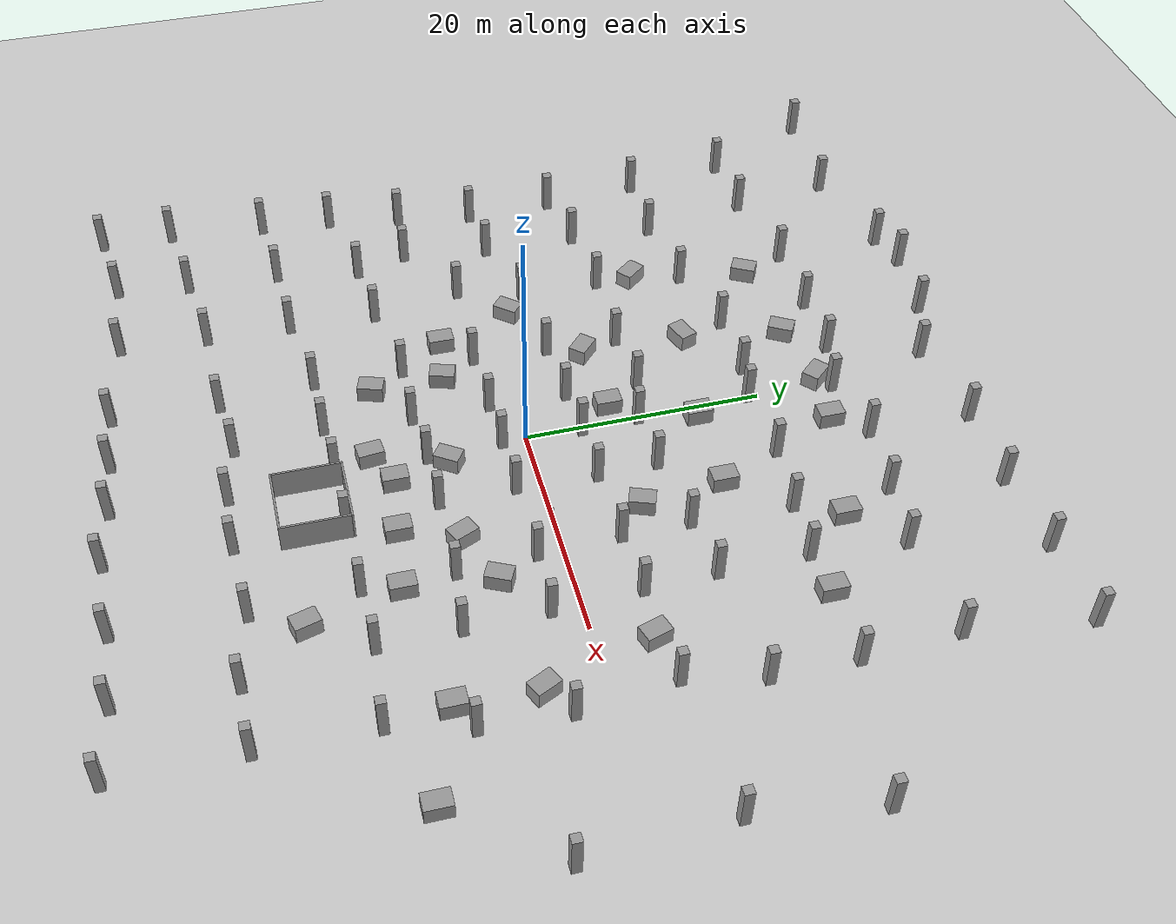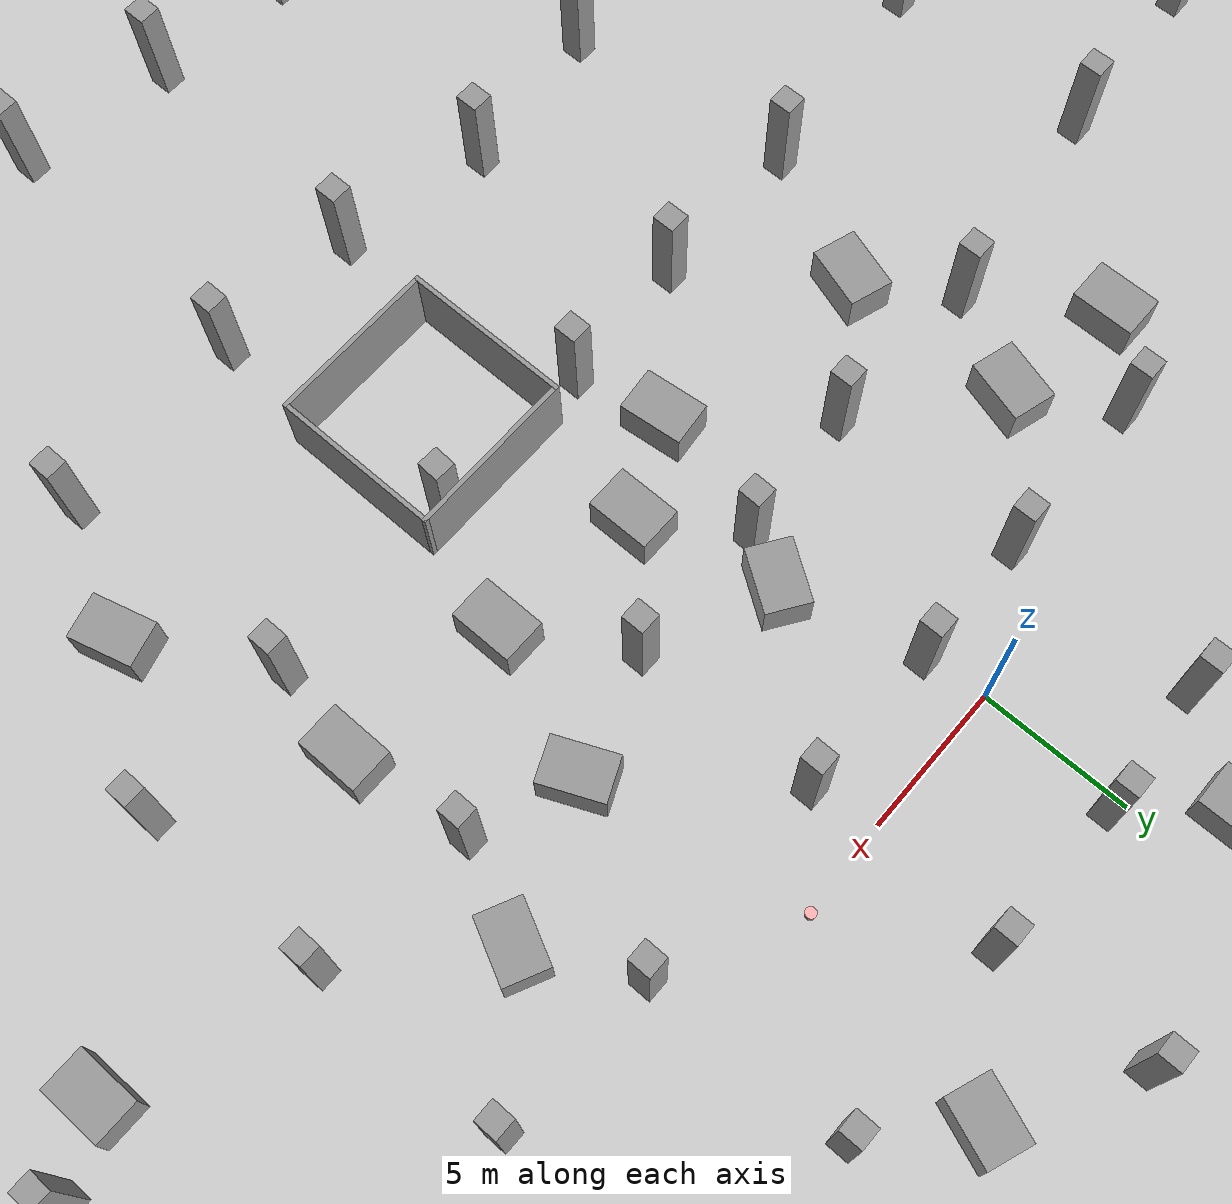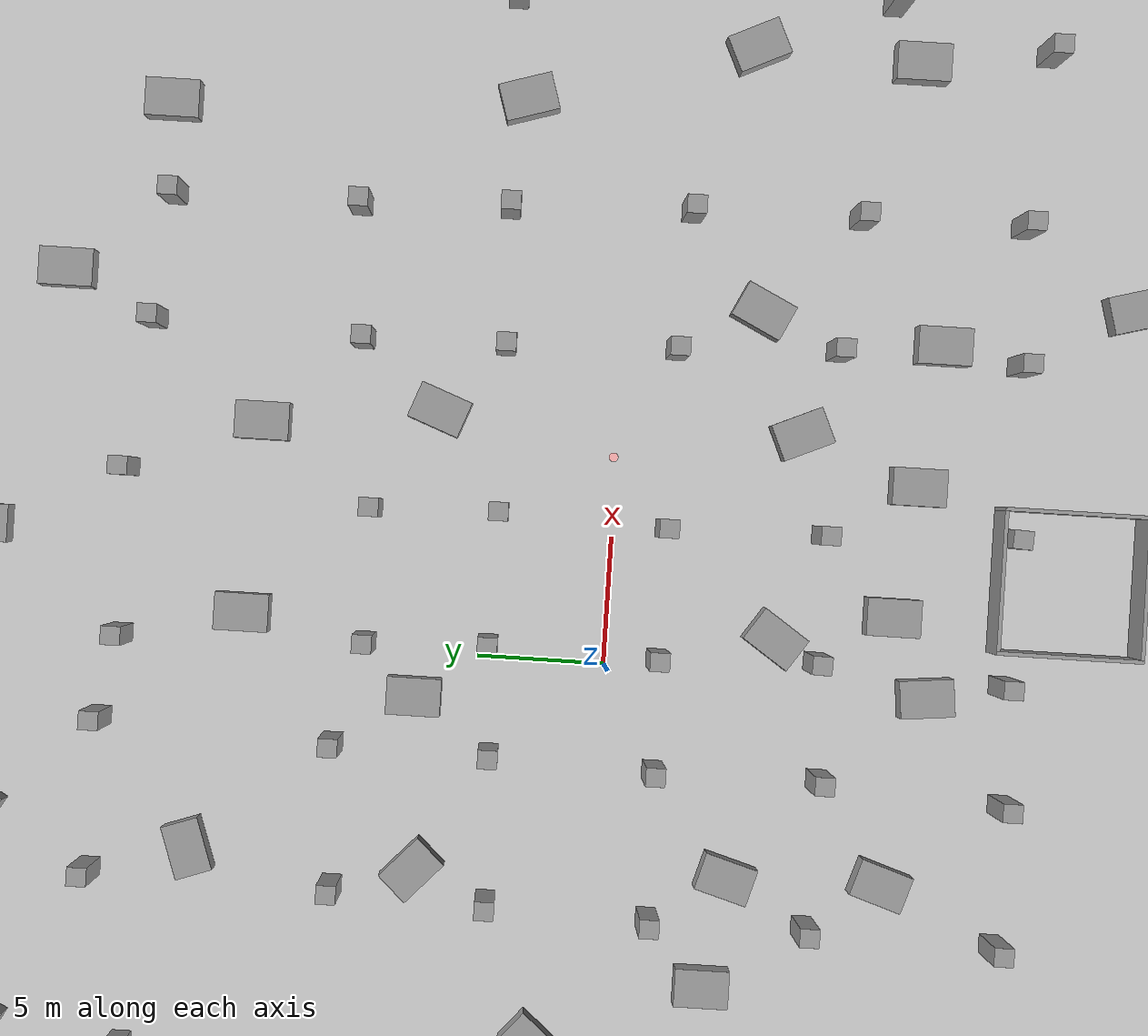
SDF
<sdf version="1.6">
 <world name="default">
  <light name="sun" type="directional">
   <pose>0 0 10 0 -0 0</pose>
   <diffuse>0.8 0.8 0.8 1</diffuse>
   <specular>0.2 0.2 0.2 1</specular>
   <attenuation>
    <range>1000</range>
    <constant>0.9</constant>
    <linear>0.01</linear>
    <quadratic>0.001</quadratic>
   </attenuation>
   <direction>-0.5 0.1 -0.9</direction>
  </light>
  <model name="ground_plane">
   <static>1</static>
   <link name="link">
    <collision name="collision">
     <geometry><plane><normal>0 0 1</normal><size>100 100</size></plane></geometry>
     <surface><friction><ode><mu>100</mu><mu2>50</mu2></ode></friction></surface>
    </collision>
    <visual name="visual">
     <cast_shadows>0</cast_shadows>
     <geometry><plane><normal>0 0 1</normal><size>100 100</size></plane></geometry>
     <material>
      <script><uri>file://media/materials/scripts/gazebo.material</uri><name>Gazebo/Grey</name></script>
     </material>
    </visual>
    <velocity_decay><linear>0</linear><angular>0</angular></velocity_decay>
   </link>
  </model>
  <physics name="default_physics" default="0" type="ode">
   <max_step_size>0.001</max_step_size>
   <real_time_factor>1</real_time_factor>
   <real_time_update_rate>1000</real_time_update_rate>
  </physics>
  <scene><ambient>0.4 0.4 0.4 1</ambient><background>0.7 0.7 0.7 1</background><shadows>1</shadows></scene>
  <spherical_coordinates>
   <surface_model>EARTH_WGS84</surface_model>
   <latitude_deg>0</latitude_deg>
   <longitude_deg>0</longitude_deg>
   <elevation>0</elevation>
   <heading_deg>0</heading_deg>
  </spherical_coordinates>
  <model name="vRoom">
   <pose>4.29627 -17.9422 0 0 -0 0</pose>
   <link name="Wall_0">
    <collision name="Wall_0_Collision">
     <geometry><box><size>5.75 0.15 2.5</size></box></geometry>
     <pose>0 0 1.25 0 -0 0</pose>
    </collision>
    <visual name="Wall_0_Visual">
     <pose>0 0 1.25 0 -0 0</pose>
     <geometry><box><size>5.75 0.15 2.5</size></box></geometry>
     <material>
      <script><uri>file://media/materials/scripts/gazebo.material</uri><name>Gazebo/Grey</name></script>
      <ambient>1 1 1 1</ambient>
     </material>
    </visual>
    <pose>-2.8 -0 0 0 0 -1.5708</pose>
    <velocity_decay><linear>0</linear><angular>0</angular></velocity_decay>
   </link>
   <link name="Wall_1">
    <collision name="Wall_1_Collision">
     <geometry><box><size>5.75 0.15 2.5</size></box></geometry>
     <pose>0 0 1.25 0 -0 0</pose>
    </collision>
    <visual name="Wall_1_Visual">
     <pose>0 0 1.25 0 -0 0</pose>
     <geometry><box><size>5.75 0.15 2.5</size></box></geometry>
     <material>
      <script><uri>file://media/materials/scripts/gazebo.material</uri><name>Gazebo/Grey</name></script>
      <ambient>1 1 1 1</ambient>
     </material>
    </visual>
    <pose>0 -2.8 0 0 -0 0</pose>
    <velocity_decay><linear>0</linear><angular>0</angular></velocity_decay>
   </link>
   <link name="Wall_2">
    <collision name="Wall_2_Collision">
     <geometry><box><size>5.75 0.15 2.5</size></box></geometry>
     <pose>0 0 1.25 0 -0 0</pose>
    </collision>
    <visual name="Wall_2_Visual">
     <pose>0 0 1.25 0 -0 0</pose>
     <geometry><box><size>5.75 0.15 2.5</size></box></geometry>
     <material>
      <script><uri>file://media/materials/scripts/gazebo.material</uri><name>Gazebo/Grey</name></script>
      <ambient>1 1 1 1</ambient>
     </material>
    </visual>
    <pose>2.8 -0 0 0 -0 1.5708</pose>
    <velocity_decay><linear>0</linear><angular>0</angular></velocity_decay>
   </link>
   <link name="Wall_3">
    <collision name="Wall_3_Collision">
     <geometry><box><size>5.75 0.15 2.5</size></box></geometry>
     <pose>0 0 1.25 0 -0 0</pose>
    </collision>
    <visual name="Wall_3_Visual">
     <pose>0 0 1.25 0 -0 0</pose>
     <geometry><box><size>5.75 0.15 2.5</size></box></geometry>
     <material>
      <script><uri>file://media/materials/scripts/gazebo.material</uri><name>Gazebo/Grey</name></script>
      <ambient>1 1 1 1</ambient>
     </material>
    </visual>
    <pose>0 2.8 0 0 -0 3.14159</pose>
    <velocity_decay><linear>0</linear><angular>0</angular></velocity_decay>
   </link>
   <static>1</static>
  </model>
  <gravity>0 0 -9.8</gravity>
  <magnetic_field>6e-06 2.3e-05 -4.2e-05</magnetic_field>
  <atmosphere type="adiabatic"/>
  <model name="unit_cylinder_15">
   <link name="link">
    <inertial>
     <mass>1</mass>
     <inertia><ixx>0.145833</ixx><ixy>0</ixy><ixz>0</ixz><iyy>0.145833</iyy><iyz>0</iyz><izz>0.125</izz></inertia>
    </inertial>
    <visual name="visual">
     <geometry><cylinder><radius>0.175793</radius><length>0.211077</length></cylinder></geometry>
     <material>
      <script><name>Gazebo/Grey</name><uri>file://media/materials/scripts/gazebo.material</uri></script>
      <ambient>1 0.3 0.3 1</ambient>
      <diffuse>1 0.7 0.7 1</diffuse>
      <specular>1 0.01 0.01 1</specular>
      <emissive>1 0 0 1</emissive>
      <shader type="vertex"><normal_map>__default__</normal_map></shader>
     </material>
    </visual>
    <collision name="collision">
     <geometry><cylinder><radius>0.175793</radius><length>0.211077</length></cylinder></geometry>
     <surface>
      <friction>
       <ode><mu>1</mu><mu2>1</mu2><fdir1>0 0 0</fdir1><slip1>0</slip1><slip2>0</slip2></ode>
       <torsional>
        <coefficient>1</coefficient>
        <patch_radius>0</patch_radius>
        <surface_radius>0</surface_radius>
        <use_patch_radius>1</use_patch_radius>
        <ode><slip>0</slip></ode>
       </torsional>
      </friction>
      <bounce><restitution_coefficient>0</restitution_coefficient><threshold>1e+06</threshold></bounce>
      <contact>
       <collide_without_contact>0</collide_without_contact>
       <collide_without_contact_bitmask>1</collide_without_contact_bitmask>
       <collide_bitmask>1</collide_bitmask>
       <ode>
        <soft_cfm>0</soft_cfm>
        <soft_erp>0.2</soft_erp>
        <kp>1e+13</kp>
        <kd>1</kd>
        <max_vel>0.01</max_vel>
        <min_depth>0</min_depth>
       </ode>
       <bullet>
        <split_impulse>1</split_impulse>
        <split_impulse_penetration_threshold>-0.01</split_impulse_penetration_threshold>
        <soft_cfm>0</soft_cfm>
        <soft_erp>0.2</soft_erp>
        <kp>1e+13</kp>
        <kd>1</kd>
       </bullet>
      </contact>
     </surface>
    </collision>
   </link>
   <static>0</static>
   <pose>8.1781 0.118835 0.105537 2e-06 -2e-06 2e-06</pose>
  </model>
  <model name="unit_box_0">
   <pose>0.552724 4.62357 1.85358 0 -0 0.000533</pose>
   <link name="link">
    <inertial>
     <mass>1</mass>
     <inertia>
      <ixx>0.166667</ixx>
      <ixy>0</ixy>
      <ixz>0</ixz>
      <iyy>0.166667</iyy>
      <iyz>0</iyz>
      <izz>0.166667</izz>
     </inertia>
    </inertial>
    <collision name="collision"><geometry><box><size>0.721478 0.765781 3.70717</size></box></geometry></collision>
    <visual name="visual">
     <geometry><box><size>0.721478 0.765781 3.70717</size></box></geometry>
     <material>
      <script><name>Gazebo/Grey</name><uri>file://media/materials/scripts/gazebo.material</uri></script>
     </material>
    </visual>
   </link>
  </model>
  <model name="unit_box_0_clone">
   <pose>5.76783 4.51377 1.85358 0 -1e-06 0.000702</pose>
   <link name="link">
    <inertial>
     <mass>1</mass>
     <inertia>
      <ixx>0.166667</ixx>
      <ixy>0</ixy>
      <ixz>0</ixz>
      <iyy>0.166667</iyy>
      <iyz>0</iyz>
      <izz>0.166667</izz>
     </inertia>
    </inertial>
    <collision name="collision"><geometry><box><size>0.721478 0.765781 3.70716</size></box></geometry></collision>
    <visual name="visual">
     <geometry><box><size>0.721478 0.765781 3.70716</size></box></geometry>
     <material>
      <script><name>Gazebo/Grey</name><uri>file://media/materials/scripts/gazebo.material</uri></script>
     </material>
    </visual>
   </link>
  </model>
  <model name="unit_box_0_clone_0">
   <pose>5.62538 9.50107 1.85358 0 -0 0.000481</pose>
   <link name="link">
    <inertial>
     <mass>1</mass>
     <inertia>
      <ixx>0.166667</ixx>
      <ixy>0</ixy>
      <ixz>0</ixz>
      <iyy>0.166667</iyy>
      <iyz>0</iyz>
      <izz>0.166667</izz>
     </inertia>
    </inertial>
    <collision name="collision"><geometry><box><size>0.721478 0.765781 3.70716</size></box></geometry></collision>
    <visual name="visual">
     <geometry><box><size>0.721478 0.765781 3.70716</size></box></geometry>
     <material>
      <script><name>Gazebo/Grey</name><uri>file://media/materials/scripts/gazebo.material</uri></script>
     </material>
    </visual>
   </link>
  </model>
  <model name="unit_box_0_clone_1">
   <pose>0.355195 9.43736 1.85358 0 -0 0.000772</pose>
   <link name="link">
    <inertial>
     <mass>1</mass>
     <inertia>
      <ixx>0.166667</ixx>
      <ixy>0</ixy>
      <ixz>0</ixz>
      <iyy>0.166667</iyy>
      <iyz>0</iyz>
      <izz>0.166667</izz>
     </inertia>
    </inertial>
    <collision name="collision"><geometry><box><size>0.721478 0.765781 3.70716</size></box></geometry></collision>
    <visual name="visual">
     <geometry><box><size>0.721478 0.765781 3.70716</size></box></geometry>
     <material>
      <script><name>Gazebo/Grey</name><uri>file://media/materials/scripts/gazebo.material</uri></script>
     </material>
    </visual>
   </link>
  </model>
  <model name="unit_box_0_clone_2">
   <pose>12.285 4.61126 1.85358 0 -0 0.000734</pose>
   <link name="link">
    <inertial>
     <mass>1</mass>
     <inertia>
      <ixx>0.166667</ixx>
      <ixy>0</ixy>
      <ixz>0</ixz>
      <iyy>0.166667</iyy>
      <iyz>0</iyz>
      <izz>0.166667</izz>
     </inertia>
    </inertial>
    <collision name="collision"><geometry><box><size>0.721478 0.765781 3.70716</size></box></geometry></collision>
    <visual name="visual">
     <geometry><box><size>0.721478 0.765781 3.70716</size></box></geometry>
     <material>
      <script><name>Gazebo/Grey</name><uri>file://media/materials/scripts/gazebo.material</uri></script>
     </material>
    </visual>
   </link>
  </model>
  <model name="unit_box_0_clone_3">
   <pose>12.2177 10.1964 1.85358 -1e-06 -0 0.000389</pose>
   <link name="link">
    <inertial>
     <mass>1</mass>
     <inertia>
      <ixx>0.166667</ixx>
      <ixy>0</ixy>
      <ixz>0</ixz>
      <iyy>0.166667</iyy>
      <iyz>0</iyz>
      <izz>0.166667</izz>
     </inertia>
    </inertial>
    <collision name="collision"><geometry><box><size>0.721478 0.765781 3.70716</size></box></geometry></collision>
    <visual name="visual">
     <geometry><box><size>0.721478 0.765781 3.70716</size></box></geometry>
     <material>
      <script><name>Gazebo/Grey</name><uri>file://media/materials/scripts/gazebo.material</uri></script>
     </material>
    </visual>
   </link>
  </model>
  <model name="unit_box_0_clone_4">
   <pose>12.5297 -2.06953 1.85358 0 -0 0.000503</pose>
   <link name="link">
    <inertial>
     <mass>1</mass>
     <inertia>
      <ixx>0.166667</ixx>
      <ixy>0</ixy>
      <ixz>0</ixz>
      <iyy>0.166667</iyy>
      <iyz>0</iyz>
      <izz>0.166667</izz>
     </inertia>
    </inertial>
    <collision name="collision"><geometry><box><size>0.721478 0.765781 3.70716</size></box></geometry></collision>
    <visual name="visual">
     <geometry><box><size>0.721478 0.765781 3.70716</size></box></geometry>
     <material>
      <script><name>Gazebo/Grey</name><uri>file://media/materials/scripts/gazebo.material</uri></script>
     </material>
    </visual>
   </link>
  </model>
  <model name="unit_box_0_clone_5">
   <pose>5.51383 -2.08188 1.85358 0 -0 0.000236</pose>
   <link name="link">
    <inertial>
     <mass>1</mass>
     <inertia>
      <ixx>0.166667</ixx>
      <ixy>0</ixy>
      <ixz>0</ixz>
      <iyy>0.166667</iyy>
      <iyz>0</iyz>
      <izz>0.166667</izz>
     </inertia>
    </inertial>
    <collision name="collision"><geometry><box><size>0.721478 0.765781 3.70716</size></box></geometry></collision>
    <visual name="visual">
     <geometry><box><size>0.721478 0.765781 3.70716</size></box></geometry>
     <material>
      <script><name>Gazebo/Grey</name><uri>file://media/materials/scripts/gazebo.material</uri></script>
     </material>
    </visual>
   </link>
  </model>
  <model name="unit_box_0_clone_6">
   <pose>0.383086 -2.03146 1.85358 1e-06 -0 0.000583</pose>
   <link name="link">
    <inertial>
     <mass>1</mass>
     <inertia>
      <ixx>0.166667</ixx>
      <ixy>0</ixy>
      <ixz>0</ixz>
      <iyy>0.166667</iyy>
      <iyz>0</iyz>
      <izz>0.166667</izz>
     </inertia>
    </inertial>
    <collision name="collision"><geometry><box><size>0.721478 0.765781 3.70716</size></box></geometry></collision>
    <visual name="visual">
     <geometry><box><size>0.721478 0.765781 3.70716</size></box></geometry>
     <material>
      <script><name>Gazebo/Grey</name><uri>file://media/materials/scripts/gazebo.material</uri></script>
     </material>
    </visual>
   </link>
  </model>
  <model name="unit_box_0_clone_7">
   <pose>12.8613 -8.40418 1.85358 0 1e-06 0.000448</pose>
   <link name="link">
    <inertial>
     <mass>1</mass>
     <inertia>
      <ixx>0.166667</ixx>
      <ixy>0</ixy>
      <ixz>0</ixz>
      <iyy>0.166667</iyy>
      <iyz>0</iyz>
      <izz>0.166667</izz>
     </inertia>
    </inertial>
    <collision name="collision"><geometry><box><size>0.721478 0.765781 3.70716</size></box></geometry></collision>
    <visual name="visual">
     <geometry><box><size>0.721478 0.765781 3.70716</size></box></geometry>
     <material>
      <script><name>Gazebo/Grey</name><uri>file://media/materials/scripts/gazebo.material</uri></script>
     </material>
    </visual>
   </link>
  </model>
  <model name="unit_box_0_clone_8">
   <pose>5.62258 -8.27771 1.85358 -1e-06 1e-06 0.000661</pose>
   <link name="link">
    <inertial>
     <mass>1</mass>
     <inertia>
      <ixx>0.166667</ixx>
      <ixy>0</ixy>
      <ixz>0</ixz>
      <iyy>0.166667</iyy>
      <iyz>0</iyz>
      <izz>0.166667</izz>
     </inertia>
    </inertial>
    <collision name="collision"><geometry><box><size>0.721478 0.765781 3.70716</size></box></geometry></collision>
    <visual name="visual">
     <geometry><box><size>0.721478 0.765781 3.70716</size></box></geometry>
     <material>
      <script><name>Gazebo/Grey</name><uri>file://media/materials/scripts/gazebo.material</uri></script>
     </material>
    </visual>
   </link>
  </model>
  <model name="unit_box_0_clone_9">
   <pose>0.635478 -8.25329 1.85358 1e-06 -0 -0.026828</pose>
   <link name="link">
    <inertial>
     <mass>1</mass>
     <inertia>
      <ixx>0.166667</ixx>
      <ixy>0</ixy>
      <ixz>0</ixz>
      <iyy>0.166667</iyy>
      <iyz>0</iyz>
      <izz>0.166667</izz>
     </inertia>
    </inertial>
    <collision name="collision"><geometry><box><size>0.721478 0.765781 3.70716</size></box></geometry></collision>
    <visual name="visual">
     <geometry><box><size>0.721478 0.765781 3.70716</size></box></geometry>
     <material>
      <script><name>Gazebo/Grey</name><uri>file://media/materials/scripts/gazebo.material</uri></script>
     </material>
    </visual>
   </link>
  </model>
  <model name="unit_box_0_clone_10">
   <pose>17.7042 4.76854 1.85358 -0 -1e-06 0.000558</pose>
   <link name="link">
    <inertial>
     <mass>1</mass>
     <inertia>
      <ixx>0.166667</ixx>
      <ixy>0</ixy>
      <ixz>0</ixz>
      <iyy>0.166667</iyy>
      <iyz>0</iyz>
      <izz>0.166667</izz>
     </inertia>
    </inertial>
    <collision name="collision"><geometry><box><size>0.721478 0.765781 3.70716</size></box></geometry></collision>
    <visual name="visual">
     <geometry><box><size>0.721478 0.765781 3.70716</size></box></geometry>
     <material>
      <script><name>Gazebo/Grey</name><uri>file://media/materials/scripts/gazebo.material</uri></script>
     </material>
    </visual>
   </link>
  </model>
  <model name="unit_box_0_clone_11">
   <pose>17.9965 -2.35859 1.85358 -1e-06 -0 0.000227</pose>
   <link name="link">
    <inertial>
     <mass>1</mass>
     <inertia>
      <ixx>0.166667</ixx>
      <ixy>0</ixy>
      <ixz>0</ixz>
      <iyy>0.166667</iyy>
      <iyz>0</iyz>
      <izz>0.166667</izz>
     </inertia>
    </inertial>
    <collision name="collision"><geometry><box><size>0.721478 0.765781 3.70716</size></box></geometry></collision>
    <visual name="visual">
     <geometry><box><size>0.721478 0.765781 3.70716</size></box></geometry>
     <material>
      <script><name>Gazebo/Grey</name><uri>file://media/materials/scripts/gazebo.material</uri></script>
     </material>
    </visual>
   </link>
  </model>
  <model name="unit_box_0_clone_12">
   <pose>18.1183 -8.99798 1.85358 0 1e-06 0.000338</pose>
   <link name="link">
    <inertial>
     <mass>1</mass>
     <inertia>
      <ixx>0.166667</ixx>
      <ixy>0</ixy>
      <ixz>0</ixz>
      <iyy>0.166667</iyy>
      <iyz>0</iyz>
      <izz>0.166667</izz>
     </inertia>
    </inertial>
    <collision name="collision"><geometry><box><size>0.721478 0.765781 3.70716</size></box></geometry></collision>
    <visual name="visual">
     <geometry><box><size>0.721478 0.765781 3.70716</size></box></geometry>
     <material>
      <script><name>Gazebo/Grey</name><uri>file://media/materials/scripts/gazebo.material</uri></script>
     </material>
    </visual>
   </link>
  </model>
  <model name="unit_box_0_clone_13">
   <pose>17.4733 10.6295 1.85358 0 -0 0.000525</pose>
   <link name="link">
    <inertial>
     <mass>1</mass>
     <inertia>
      <ixx>0.166667</ixx>
      <ixy>0</ixy>
      <ixz>0</ixz>
      <iyy>0.166667</iyy>
      <iyz>0</iyz>
      <izz>0.166667</izz>
     </inertia>
    </inertial>
    <collision name="collision"><geometry><box><size>0.721478 0.765781 3.70716</size></box></geometry></collision>
    <visual name="visual">
     <geometry><box><size>0.721478 0.765781 3.70716</size></box></geometry>
     <material>
      <script><name>Gazebo/Grey</name><uri>file://media/materials/scripts/gazebo.material</uri></script>
     </material>
    </visual>
   </link>
  </model>
  <model name="unit_box_0_clone_14">
   <pose>17.4477 17.9556 1.85358 0 1e-06 0.000406</pose>
   <link name="link">
    <inertial>
     <mass>1</mass>
     <inertia>
      <ixx>0.166667</ixx>
      <ixy>0</ixy>
      <ixz>0</ixz>
      <iyy>0.166667</iyy>
      <iyz>0</iyz>
      <izz>0.166667</izz>
     </inertia>
    </inertial>
    <collision name="collision"><geometry><box><size>0.721478 0.765781 3.70716</size></box></geometry></collision>
    <visual name="visual">
     <geometry><box><size>0.721478 0.765781 3.70716</size></box></geometry>
     <material>
      <script><name>Gazebo/Grey</name><uri>file://media/materials/scripts/gazebo.material</uri></script>
     </material>
    </visual>
   </link>
  </model>
  <model name="unit_box_0_clone_15">
   <pose>12.5152 18.4395 1.85358 -1e-06 -0 0.000385</pose>
   <link name="link">
    <inertial>
     <mass>1</mass>
     <inertia>
      <ixx>0.166667</ixx>
      <ixy>0</ixy>
      <ixz>0</ixz>
      <iyy>0.166667</iyy>
      <iyz>0</iyz>
      <izz>0.166667</izz>
     </inertia>
    </inertial>
    <collision name="collision"><geometry><box><size>0.721478 0.765781 3.70716</size></box></geometry></collision>
    <visual name="visual">
     <geometry><box><size>0.721478 0.765781 3.70716</size></box></geometry>
     <material>
      <script><name>Gazebo/Grey</name><uri>file://media/materials/scripts/gazebo.material</uri></script>
     </material>
    </visual>
   </link>
  </model>
  <model name="unit_box_0_clone_16">
   <pose>6.631 19.1983 1.85358 0 -0 0.000638</pose>
   <link name="link">
    <inertial>
     <mass>1</mass>
     <inertia>
      <ixx>0.166667</ixx>
      <ixy>0</ixy>
      <ixz>0</ixz>
      <iyy>0.166667</iyy>
      <iyz>0</iyz>
      <izz>0.166667</izz>
     </inertia>
    </inertial>
    <collision name="collision"><geometry><box><size>0.721478 0.765781 3.70716</size></box></geometry></collision>
    <visual name="visual">
     <geometry><box><size>0.721478 0.765781 3.70716</size></box></geometry>
     <material>
      <script><name>Gazebo/Grey</name><uri>file://media/materials/scripts/gazebo.material</uri></script>
     </material>
    </visual>
   </link>
  </model>
  <model name="unit_box_0_clone_17">
   <pose>0.089127 19.0632 1.85358 0 -0 0.000226</pose>
   <link name="link">
    <inertial>
     <mass>1</mass>
     <inertia>
      <ixx>0.166667</ixx>
      <ixy>0</ixy>
      <ixz>0</ixz>
      <iyy>0.166667</iyy>
      <iyz>0</iyz>
      <izz>0.166667</izz>
     </inertia>
    </inertial>
    <collision name="collision"><geometry><box><size>0.721478 0.765781 3.70716</size></box></geometry></collision>
    <visual name="visual">
     <geometry><box><size>0.721478 0.765781 3.70716</size></box></geometry>
     <material>
      <script><name>Gazebo/Grey</name><uri>file://media/materials/scripts/gazebo.material</uri></script>
     </material>
    </visual>
   </link>
  </model>
  <model name="unit_box_0_clone_18">
   <pose>18.1486 25.5936 1.85358 0 1e-06 0.000392</pose>
   <link name="link">
    <inertial>
     <mass>1</mass>
     <inertia>
      <ixx>0.166667</ixx>
      <ixy>0</ixy>
      <ixz>0</ixz>
      <iyy>0.166667</iyy>
      <iyz>0</iyz>
      <izz>0.166667</izz>
     </inertia>
    </inertial>
    <collision name="collision"><geometry><box><size>0.721478 0.765781 3.70716</size></box></geometry></collision>
    <visual name="visual">
     <geometry><box><size>0.721478 0.765781 3.70716</size></box></geometry>
     <material>
      <script><name>Gazebo/Grey</name><uri>file://media/materials/scripts/gazebo.material</uri></script>
     </material>
    </visual>
   </link>
  </model>
  <model name="unit_box_0_clone_19">
   <pose>12.5778 26.4061 1.85358 0 -0 0.000368</pose>
   <link name="link">
    <inertial>
     <mass>1</mass>
     <inertia>
      <ixx>0.166667</ixx>
      <ixy>0</ixy>
      <ixz>0</ixz>
      <iyy>0.166667</iyy>
      <iyz>0</iyz>
      <izz>0.166667</izz>
     </inertia>
    </inertial>
    <collision name="collision"><geometry><box><size>0.721478 0.765781 3.70716</size></box></geometry></collision>
    <visual name="visual">
     <geometry><box><size>0.721478 0.765781 3.70716</size></box></geometry>
     <material>
      <script><name>Gazebo/Grey</name><uri>file://media/materials/scripts/gazebo.material</uri></script>
     </material>
    </visual>
   </link>
  </model>
  <model name="unit_box_0_clone_20">
   <pose>6.38944 27.3213 1.85358 0 -0 0.00041</pose>
   <link name="link">
    <inertial>
     <mass>1</mass>
     <inertia>
      <ixx>0.166667</ixx>
      <ixy>0</ixy>
      <ixz>0</ixz>
      <iyy>0.166667</iyy>
      <iyz>0</iyz>
      <izz>0.166667</izz>
     </inertia>
    </inertial>
    <collision name="collision"><geometry><box><size>0.721478 0.765781 3.70716</size></box></geometry></collision>
    <visual name="visual">
     <geometry><box><size>0.721478 0.765781 3.70716</size></box></geometry>
     <material>
      <script><name>Gazebo/Grey</name><uri>file://media/materials/scripts/gazebo.material</uri></script>
     </material>
    </visual>
   </link>
  </model>
  <model name="unit_box_0_clone_21">
   <pose>0.542146 26.3372 1.85358 -1e-06 0 0.000363</pose>
   <link name="link">
    <inertial>
     <mass>1</mass>
     <inertia>
      <ixx>0.166667</ixx>
      <ixy>0</ixy>
      <ixz>0</ixz>
      <iyy>0.166667</iyy>
      <iyz>0</iyz>
      <izz>0.166667</izz>
     </inertia>
    </inertial>
    <collision name="collision"><geometry><box><size>0.721478 0.765781 3.70716</size></box></geometry></collision>
    <visual name="visual">
     <geometry><box><size>0.721478 0.765781 3.70716</size></box></geometry>
     <material>
      <script><name>Gazebo/Grey</name><uri>file://media/materials/scripts/gazebo.material</uri></script>
     </material>
    </visual>
   </link>
  </model>
  <model name="unit_box_0_clone_22">
   <pose>18.1659 -15.412 1.85358 1e-06 -0 0.000373</pose>
   <link name="link">
    <inertial>
     <mass>1</mass>
     <inertia>
      <ixx>0.166667</ixx>
      <ixy>0</ixy>
      <ixz>0</ixz>
      <iyy>0.166667</iyy>
      <iyz>0</iyz>
      <izz>0.166667</izz>
     </inertia>
    </inertial>
    <collision name="collision"><geometry><box><size>0.721478 0.765781 3.70716</size></box></geometry></collision>
    <visual name="visual">
     <geometry><box><size>0.721478 0.765781 3.70716</size></box></geometry>
     <material>
      <script><name>Gazebo/Grey</name><uri>file://media/materials/scripts/gazebo.material</uri></script>
     </material>
    </visual>
   </link>
  </model>
  <model name="unit_box_0_clone_23">
   <pose>12.7073 -15.5893 1.85358 0 -1e-06 0.000288</pose>
   <link name="link">
    <inertial>
     <mass>1</mass>
     <inertia>
      <ixx>0.166667</ixx>
      <ixy>0</ixy>
      <ixz>0</ixz>
      <iyy>0.166667</iyy>
      <iyz>0</iyz>
      <izz>0.166667</izz>
     </inertia>
    </inertial>
    <collision name="collision"><geometry><box><size>0.721478 0.765781 3.70716</size></box></geometry></collision>
    <visual name="visual">
     <geometry><box><size>0.721478 0.765781 3.70716</size></box></geometry>
     <material>
      <script><name>Gazebo/Grey</name><uri>file://media/materials/scripts/gazebo.material</uri></script>
     </material>
    </visual>
   </link>
  </model>
  <model name="unit_box_0_clone_24">
   <pose>5.93577 -15.631 1.85358 1e-06 -0 -0.053246</pose>
   <link name="link">
    <inertial>
     <mass>1</mass>
     <inertia>
      <ixx>0.166667</ixx>
      <ixy>0</ixy>
      <ixz>0</ixz>
      <iyy>0.166667</iyy>
      <iyz>0</iyz>
      <izz>0.166667</izz>
     </inertia>
    </inertial>
    <collision name="collision"><geometry><box><size>0.721478 0.765781 3.70716</size></box></geometry></collision>
    <visual name="visual">
     <geometry><box><size>0.721478 0.765781 3.70716</size></box></geometry>
     <material>
      <script><name>Gazebo/Grey</name><uri>file://media/materials/scripts/gazebo.material</uri></script>
     </material>
    </visual>
   </link>
  </model>
  <model name="unit_box_0_clone_25">
   <pose>0.139528 -15.6324 1.85358 0 -0 0.000554</pose>
   <link name="link">
    <inertial>
     <mass>1</mass>
     <inertia>
      <ixx>0.166667</ixx>
      <ixy>0</ixy>
      <ixz>0</ixz>
      <iyy>0.166667</iyy>
      <iyz>0</iyz>
      <izz>0.166667</izz>
     </inertia>
    </inertial>
    <collision name="collision"><geometry><box><size>0.721478 0.765781 3.70716</size></box></geometry></collision>
    <visual name="visual">
     <geometry><box><size>0.721478 0.765781 3.70716</size></box></geometry>
     <material>
      <script><name>Gazebo/Grey</name><uri>file://media/materials/scripts/gazebo.material</uri></script>
     </material>
    </visual>
   </link>
  </model>
  <model name="unit_box_0_clone_26">
   <pose>-3.983 -8.63798 1.85358 0 1e-06 0.000534</pose>
   <link name="link">
    <inertial>
     <mass>1</mass>
     <inertia>
      <ixx>0.166667</ixx>
      <ixy>0</ixy>
      <ixz>0</ixz>
      <iyy>0.166667</iyy>
      <iyz>0</iyz>
      <izz>0.166667</izz>
     </inertia>
    </inertial>
    <collision name="collision"><geometry><box><size>0.721478 0.765781 3.70716</size></box></geometry></collision>
    <visual name="visual">
     <geometry><box><size>0.721478 0.765781 3.70716</size></box></geometry>
     <material>
      <script><name>Gazebo/Grey</name><uri>file://media/materials/scripts/gazebo.material</uri></script>
     </material>
    </visual>
   </link>
  </model>
  <model name="unit_box_0_clone_27">
   <pose>-4.03126 -2.1358 1.85358 0 -1e-06 0.000593</pose>
   <link name="link">
    <inertial>
     <mass>1</mass>
     <inertia>
      <ixx>0.166667</ixx>
      <ixy>0</ixy>
      <ixz>0</ixz>
      <iyy>0.166667</iyy>
      <iyz>0</iyz>
      <izz>0.166667</izz>
     </inertia>
    </inertial>
    <collision name="collision"><geometry><box><size>0.721478 0.765781 3.70716</size></box></geometry></collision>
    <visual name="visual">
     <geometry><box><size>0.721478 0.765781 3.70716</size></box></geometry>
     <material>
      <script><name>Gazebo/Grey</name><uri>file://media/materials/scripts/gazebo.material</uri></script>
     </material>
    </visual>
   </link>
  </model>
  <model name="unit_box_0_clone_28">
   <pose>-3.75851 4.34526 1.85358 -1e-06 0 0.000588</pose>
   <link name="link">
    <inertial>
     <mass>1</mass>
     <inertia>
      <ixx>0.166667</ixx>
      <ixy>0</ixy>
      <ixz>0</ixz>
      <iyy>0.166667</iyy>
      <iyz>0</iyz>
      <izz>0.166667</izz>
     </inertia>
    </inertial>
    <collision name="collision"><geometry><box><size>0.721478 0.765781 3.70716</size></box></geometry></collision>
    <visual name="visual">
     <geometry><box><size>0.721478 0.765781 3.70716</size></box></geometry>
     <material>
      <script><name>Gazebo/Grey</name><uri>file://media/materials/scripts/gazebo.material</uri></script>
     </material>
    </visual>
   </link>
  </model>
  <model name="unit_box_0_clone_29">
   <pose>-3.69631 10.4945 1.85358 0 -0 0.000566</pose>
   <link name="link">
    <inertial>
     <mass>1</mass>
     <inertia>
      <ixx>0.166667</ixx>
      <ixy>0</ixy>
      <ixz>0</ixz>
      <iyy>0.166667</iyy>
      <iyz>0</iyz>
      <izz>0.166667</izz>
     </inertia>
    </inertial>
    <collision name="collision"><geometry><box><size>0.721478 0.765781 3.70716</size></box></geometry></collision>
    <visual name="visual">
     <geometry><box><size>0.721478 0.765781 3.70716</size></box></geometry>
     <material>
      <script><name>Gazebo/Grey</name><uri>file://media/materials/scripts/gazebo.material</uri></script>
     </material>
    </visual>
   </link>
  </model>
  <model name="unit_box_0_clone_30">
   <pose>-4.55169 -15.8841 1.85358 0 -0 0.000663</pose>
   <link name="link">
    <inertial>
     <mass>1</mass>
     <inertia>
      <ixx>0.166667</ixx>
      <ixy>0</ixy>
      <ixz>0</ixz>
      <iyy>0.166667</iyy>
      <iyz>0</iyz>
      <izz>0.166667</izz>
     </inertia>
    </inertial>
    <collision name="collision"><geometry><box><size>0.721478 0.765781 3.70716</size></box></geometry></collision>
    <visual name="visual">
     <geometry><box><size>0.721478 0.765781 3.70716</size></box></geometry>
     <material>
      <script><name>Gazebo/Grey</name><uri>file://media/materials/scripts/gazebo.material</uri></script>
     </material>
    </visual>
   </link>
  </model>
  <model name="unit_box_0_clone_31">
   <pose>-3.21677 19.7035 1.85358 0 -0 0.000511</pose>
   <link name="link">
    <inertial>
     <mass>1</mass>
     <inertia>
      <ixx>0.166667</ixx>
      <ixy>0</ixy>
      <ixz>0</ixz>
      <iyy>0.166667</iyy>
      <iyz>0</iyz>
      <izz>0.166667</izz>
     </inertia>
    </inertial>
    <collision name="collision"><geometry><box><size>0.721478 0.765781 3.70716</size></box></geometry></collision>
    <visual name="visual">
     <geometry><box><size>0.721478 0.765781 3.70716</size></box></geometry>
     <material>
      <script><name>Gazebo/Grey</name><uri>file://media/materials/scripts/gazebo.material</uri></script>
     </material>
    </visual>
   </link>
  </model>
  <model name="unit_box_0_clone_32">
   <pose>-4.10112 27.6439 1.85358 0 -0 0.000603</pose>
   <link name="link">
    <inertial>
     <mass>1</mass>
     <inertia>
      <ixx>0.166667</ixx>
      <ixy>0</ixy>
      <ixz>0</ixz>
      <iyy>0.166667</iyy>
      <iyz>0</iyz>
      <izz>0.166667</izz>
     </inertia>
    </inertial>
    <collision name="collision"><geometry><box><size>0.721478 0.765781 3.70716</size></box></geometry></collision>
    <visual name="visual">
     <geometry><box><size>0.721478 0.765781 3.70716</size></box></geometry>
     <material>
      <script><name>Gazebo/Grey</name><uri>file://media/materials/scripts/gazebo.material</uri></script>
     </material>
    </visual>
   </link>
  </model>
  <model name="unit_box_0_clone_33">
   <pose>-10.0764 -15.8876 1.85358 0 -0 0.000475</pose>
   <link name="link">
    <inertial>
     <mass>1</mass>
     <inertia>
      <ixx>0.166667</ixx>
      <ixy>0</ixy>
      <ixz>0</ixz>
      <iyy>0.166667</iyy>
      <iyz>0</iyz>
      <izz>0.166667</izz>
     </inertia>
    </inertial>
    <collision name="collision"><geometry><box><size>0.721478 0.765781 3.70716</size></box></geometry></collision>
    <visual name="visual">
     <geometry><box><size>0.721478 0.765781 3.70716</size></box></geometry>
     <material>
      <script><name>Gazebo/Grey</name><uri>file://media/materials/scripts/gazebo.material</uri></script>
     </material>
    </visual>
   </link>
  </model>
  <model name="unit_box_0_clone_34">
   <pose>-9.80887 -8.41238 1.85358 1e-06 0 0.000303</pose>
   <link name="link">
    <inertial>
     <mass>1</mass>
     <inertia>
      <ixx>0.166667</ixx>
      <ixy>0</ixy>
      <ixz>0</ixz>
      <iyy>0.166667</iyy>
      <iyz>0</iyz>
      <izz>0.166667</izz>
     </inertia>
    </inertial>
    <collision name="collision"><geometry><box><size>0.721478 0.765781 3.70716</size></box></geometry></collision>
    <visual name="visual">
     <geometry><box><size>0.721478 0.765781 3.70716</size></box></geometry>
     <material>
      <script><name>Gazebo/Grey</name><uri>file://media/materials/scripts/gazebo.material</uri></script>
     </material>
    </visual>
   </link>
  </model>
  <model name="unit_box_0_clone_35">
   <pose>-9.84797 -2.25043 1.85358 -1e-06 -0 0.000566</pose>
   <link name="link">
    <inertial>
     <mass>1</mass>
     <inertia>
      <ixx>0.166667</ixx>
      <ixy>0</ixy>
      <ixz>0</ixz>
      <iyy>0.166667</iyy>
      <iyz>0</iyz>
      <izz>0.166667</izz>
     </inertia>
    </inertial>
    <collision name="collision"><geometry><box><size>0.721478 0.765781 3.70716</size></box></geometry></collision>
    <visual name="visual">
     <geometry><box><size>0.721478 0.765781 3.70716</size></box></geometry>
     <material>
      <script><name>Gazebo/Grey</name><uri>file://media/materials/scripts/gazebo.material</uri></script>
     </material>
    </visual>
   </link>
  </model>
  <model name="unit_box_0_clone_36">
   <pose>-9.559 4.11578 1.85358 0 1e-06 0.000651</pose>
   <link name="link">
    <inertial>
     <mass>1</mass>
     <inertia>
      <ixx>0.166667</ixx>
      <ixy>0</ixy>
      <ixz>0</ixz>
      <iyy>0.166667</iyy>
      <iyz>0</iyz>
      <izz>0.166667</izz>
     </inertia>
    </inertial>
    <collision name="collision"><geometry><box><size>0.721478 0.765781 3.70716</size></box></geometry></collision>
    <visual name="visual">
     <geometry><box><size>0.721478 0.765781 3.70716</size></box></geometry>
     <material>
      <script><name>Gazebo/Grey</name><uri>file://media/materials/scripts/gazebo.material</uri></script>
     </material>
    </visual>
   </link>
  </model>
  <model name="unit_box_0_clone_37">
   <pose>-9.31238 10.2072 1.85358 1e-06 0 0.000324</pose>
   <link name="link">
    <inertial>
     <mass>1</mass>
     <inertia>
      <ixx>0.166667</ixx>
      <ixy>0</ixy>
      <ixz>0</ixz>
      <iyy>0.166667</iyy>
      <iyz>0</iyz>
      <izz>0.166667</izz>
     </inertia>
    </inertial>
    <collision name="collision"><geometry><box><size>0.721478 0.765781 3.70716</size></box></geometry></collision>
    <visual name="visual">
     <geometry><box><size>0.721478 0.765781 3.70716</size></box></geometry>
     <material>
      <script><name>Gazebo/Grey</name><uri>file://media/materials/scripts/gazebo.material</uri></script>
     </material>
    </visual>
   </link>
  </model>
  <model name="unit_box_0_clone_38">
   <pose>-9.21908 19.7816 1.85358 -1e-06 -0 0.000661</pose>
   <link name="link">
    <inertial>
     <mass>1</mass>
     <inertia>
      <ixx>0.166667</ixx>
      <ixy>0</ixy>
      <ixz>0</ixz>
      <iyy>0.166667</iyy>
      <iyz>0</iyz>
      <izz>0.166667</izz>
     </inertia>
    </inertial>
    <collision name="collision"><geometry><box><size>0.721478 0.765781 3.70716</size></box></geometry></collision>
    <visual name="visual">
     <geometry><box><size>0.721478 0.765781 3.70716</size></box></geometry>
     <material>
      <script><name>Gazebo/Grey</name><uri>file://media/materials/scripts/gazebo.material</uri></script>
     </material>
    </visual>
   </link>
  </model>
  <model name="unit_box_0_clone_39">
   <pose>-9.97058 27.8436 1.85358 1e-06 -0 0.000582</pose>
   <link name="link">
    <inertial>
     <mass>1</mass>
     <inertia>
      <ixx>0.166667</ixx>
      <ixy>0</ixy>
      <ixz>0</ixz>
      <iyy>0.166667</iyy>
      <iyz>0</iyz>
      <izz>0.166667</izz>
     </inertia>
    </inertial>
    <collision name="collision"><geometry><box><size>0.721478 0.765781 3.70716</size></box></geometry></collision>
    <visual name="visual">
     <geometry><box><size>0.721478 0.765781 3.70716</size></box></geometry>
     <material>
      <script><name>Gazebo/Grey</name><uri>file://media/materials/scripts/gazebo.material</uri></script>
     </material>
    </visual>
   </link>
  </model>
  <model name="unit_box_0_clone_40">
   <pose>-17.4 -9.48121 1.85358 -1e-06 -0 0.000379</pose>
   <link name="link">
    <inertial>
     <mass>1</mass>
     <inertia>
      <ixx>0.166667</ixx>
      <ixy>0</ixy>
      <ixz>0</ixz>
      <iyy>0.166667</iyy>
      <iyz>0</iyz>
      <izz>0.166667</izz>
     </inertia>
    </inertial>
    <collision name="collision"><geometry><box><size>0.721478 0.765781 3.70716</size></box></geometry></collision>
    <visual name="visual">
     <geometry><box><size>0.721478 0.765781 3.70716</size></box></geometry>
     <material>
      <script><name>Gazebo/Grey</name><uri>file://media/materials/scripts/gazebo.material</uri></script>
     </material>
    </visual>
   </link>
  </model>
  <model name="unit_box_0_clone_41">
   <pose>-17.6338 -16.9069 1.85358 0 -0 0.000554</pose>
   <link name="link">
    <inertial>
     <mass>1</mass>
     <inertia>
      <ixx>0.166667</ixx>
      <ixy>0</ixy>
      <ixz>0</ixz>
      <iyy>0.166667</iyy>
      <iyz>0</iyz>
      <izz>0.166667</izz>
     </inertia>
    </inertial>
    <collision name="collision"><geometry><box><size>0.721478 0.765781 3.70716</size></box></geometry></collision>
    <visual name="visual">
     <geometry><box><size>0.721478 0.765781 3.70716</size></box></geometry>
     <material>
      <script><name>Gazebo/Grey</name><uri>file://media/materials/scripts/gazebo.material</uri></script>
     </material>
    </visual>
   </link>
  </model>
  <model name="unit_box_0_clone_42">
   <pose>-18.7564 -1.80751 1.85358 -0 -1e-06 0.000684</pose>
   <link name="link">
    <inertial>
     <mass>1</mass>
     <inertia>
      <ixx>0.166667</ixx>
      <ixy>0</ixy>
      <ixz>0</ixz>
      <iyy>0.166667</iyy>
      <iyz>0</iyz>
      <izz>0.166667</izz>
     </inertia>
    </inertial>
    <collision name="collision"><geometry><box><size>0.721478 0.765781 3.70716</size></box></geometry></collision>
    <visual name="visual">
     <geometry><box><size>0.721478 0.765781 3.70716</size></box></geometry>
     <material>
      <script><name>Gazebo/Grey</name><uri>file://media/materials/scripts/gazebo.material</uri></script>
     </material>
    </visual>
   </link>
  </model>
  <model name="unit_box_0_clone_43">
   <pose>-17.2028 3.77187 1.85358 -0 -1e-06 0.000669</pose>
   <link name="link">
    <inertial>
     <mass>1</mass>
     <inertia>
      <ixx>0.166667</ixx>
      <ixy>0</ixy>
      <ixz>0</ixz>
      <iyy>0.166667</iyy>
      <iyz>0</iyz>
      <izz>0.166667</izz>
     </inertia>
    </inertial>
    <collision name="collision"><geometry><box><size>0.721478 0.765781 3.70716</size></box></geometry></collision>
    <visual name="visual">
     <geometry><box><size>0.721478 0.765781 3.70716</size></box></geometry>
     <material>
      <script><name>Gazebo/Grey</name><uri>file://media/materials/scripts/gazebo.material</uri></script>
     </material>
    </visual>
   </link>
  </model>
  <model name="unit_box_0_clone_44">
   <pose>-17.0616 10.6374 1.85358 0 -0 0.000725</pose>
   <link name="link">
    <inertial>
     <mass>1</mass>
     <inertia>
      <ixx>0.166667</ixx>
      <ixy>0</ixy>
      <ixz>0</ixz>
      <iyy>0.166667</iyy>
      <iyz>0</iyz>
      <izz>0.166667</izz>
     </inertia>
    </inertial>
    <collision name="collision"><geometry><box><size>0.721478 0.765781 3.70716</size></box></geometry></collision>
    <visual name="visual">
     <geometry><box><size>0.721478 0.765781 3.70716</size></box></geometry>
     <material>
      <script><name>Gazebo/Grey</name><uri>file://media/materials/scripts/gazebo.material</uri></script>
     </material>
    </visual>
   </link>
  </model>
  <model name="unit_box_0_clone_45">
   <pose>-16.0137 18.1359 1.85358 -1e-06 -0 0.000697</pose>
   <link name="link">
    <inertial>
     <mass>1</mass>
     <inertia>
      <ixx>0.166667</ixx>
      <ixy>0</ixy>
      <ixz>0</ixz>
      <iyy>0.166667</iyy>
      <iyz>0</iyz>
      <izz>0.166667</izz>
     </inertia>
    </inertial>
    <collision name="collision"><geometry><box><size>0.721478 0.765781 3.70716</size></box></geometry></collision>
    <visual name="visual">
     <geometry><box><size>0.721478 0.765781 3.70716</size></box></geometry>
     <material>
      <script><name>Gazebo/Grey</name><uri>file://media/materials/scripts/gazebo.material</uri></script>
     </material>
    </visual>
   </link>
  </model>
  <model name="unit_box_0_clone_46">
   <pose>-16.7202 27.9817 1.85358 -1e-06 -0 0.000438</pose>
   <link name="link">
    <inertial>
     <mass>1</mass>
     <inertia>
      <ixx>0.166667</ixx>
      <ixy>0</ixy>
      <ixz>0</ixz>
      <iyy>0.166667</iyy>
      <iyz>0</iyz>
      <izz>0.166667</izz>
     </inertia>
    </inertial>
    <collision name="collision"><geometry><box><size>0.721478 0.765781 3.70716</size></box></geometry></collision>
    <visual name="visual">
     <geometry><box><size>0.721478 0.765781 3.70716</size></box></geometry>
     <material>
      <script><name>Gazebo/Grey</name><uri>file://media/materials/scripts/gazebo.material</uri></script>
     </material>
    </visual>
   </link>
  </model>
  <model name="unit_box_0_clone_47">
   <pose>-24.8994 26.7733 1.85358 0 -1e-06 0.000408</pose>
   <link name="link">
    <inertial>
     <mass>1</mass>
     <inertia>
      <ixx>0.166667</ixx>
      <ixy>0</ixy>
      <ixz>0</ixz>
      <iyy>0.166667</iyy>
      <iyz>0</iyz>
      <izz>0.166667</izz>
     </inertia>
    </inertial>
    <collision name="collision"><geometry><box><size>0.721478 0.765781 3.70716</size></box></geometry></collision>
    <visual name="visual">
     <geometry><box><size>0.721478 0.765781 3.70716</size></box></geometry>
     <material>
      <script><name>Gazebo/Grey</name><uri>file://media/materials/scripts/gazebo.material</uri></script>
     </material>
    </visual>
   </link>
  </model>
  <model name="unit_box_0_clone_48">
   <pose>-23.3545 17.3987 1.85358 0 -1e-06 0.000656</pose>
   <link name="link">
    <inertial>
     <mass>1</mass>
     <inertia>
      <ixx>0.166667</ixx>
      <ixy>0</ixy>
      <ixz>0</ixz>
      <iyy>0.166667</iyy>
      <iyz>0</iyz>
      <izz>0.166667</izz>
     </inertia>
    </inertial>
    <collision name="collision"><geometry><box><size>0.721478 0.765781 3.70716</size></box></geometry></collision>
    <visual name="visual">
     <geometry><box><size>0.721478 0.765781 3.70716</size></box></geometry>
     <material>
      <script><name>Gazebo/Grey</name><uri>file://media/materials/scripts/gazebo.material</uri></script>
     </material>
    </visual>
   </link>
  </model>
  <model name="unit_box_0_clone_49">
   <pose>-23.8608 10.1213 1.85358 0 -1e-06 0.000806</pose>
   <link name="link">
    <inertial>
     <mass>1</mass>
     <inertia>
      <ixx>0.166667</ixx>
      <ixy>0</ixy>
      <ixz>0</ixz>
      <iyy>0.166667</iyy>
      <iyz>0</iyz>
      <izz>0.166667</izz>
     </inertia>
    </inertial>
    <collision name="collision"><geometry><box><size>0.721478 0.765781 3.70716</size></box></geometry></collision>
    <visual name="visual">
     <geometry><box><size>0.721478 0.765781 3.70716</size></box></geometry>
     <material>
      <script><name>Gazebo/Grey</name><uri>file://media/materials/scripts/gazebo.material</uri></script>
     </material>
    </visual>
   </link>
  </model>
  <model name="unit_box_0_clone_50">
   <pose>-23.9772 1.98235 1.85358 -0 1e-06 0.000303</pose>
   <link name="link">
    <inertial>
     <mass>1</mass>
     <inertia>
      <ixx>0.166667</ixx>
      <ixy>0</ixy>
      <ixz>0</ixz>
      <iyy>0.166667</iyy>
      <iyz>0</iyz>
      <izz>0.166667</izz>
     </inertia>
    </inertial>
    <collision name="collision"><geometry><box><size>0.721478 0.765781 3.70716</size></box></geometry></collision>
    <visual name="visual">
     <geometry><box><size>0.721478 0.765781 3.70716</size></box></geometry>
     <material>
      <script><name>Gazebo/Grey</name><uri>file://media/materials/scripts/gazebo.material</uri></script>
     </material>
    </visual>
   </link>
  </model>
  <model name="unit_box_0_clone_51">
   <pose>-25.018 -5.48743 1.85358 0 -0 0.000438</pose>
   <link name="link">
    <inertial>
     <mass>1</mass>
     <inertia>
      <ixx>0.166667</ixx>
      <ixy>0</ixy>
      <ixz>0</ixz>
      <iyy>0.166667</iyy>
      <iyz>0</iyz>
      <izz>0.166667</izz>
     </inertia>
    </inertial>
    <collision name="collision"><geometry><box><size>0.721478 0.765781 3.70716</size></box></geometry></collision>
    <visual name="visual">
     <geometry><box><size>0.721478 0.765781 3.70716</size></box></geometry>
     <material>
      <script><name>Gazebo/Grey</name><uri>file://media/materials/scripts/gazebo.material</uri></script>
     </material>
    </visual>
   </link>
  </model>
  <model name="unit_box_0_clone_52">
   <pose>-23.6786 -9.95656 1.85358 -0 -1e-06 0.000425</pose>
   <link name="link">
    <inertial>
     <mass>1</mass>
     <inertia>
      <ixx>0.166667</ixx>
      <ixy>0</ixy>
      <ixz>0</ixz>
      <iyy>0.166667</iyy>
      <iyz>0</iyz>
      <izz>0.166667</izz>
     </inertia>
    </inertial>
    <collision name="collision"><geometry><box><size>0.721478 0.765781 3.70716</size></box></geometry></collision>
    <visual name="visual">
     <geometry><box><size>0.721478 0.765781 3.70716</size></box></geometry>
     <material>
      <script><name>Gazebo/Grey</name><uri>file://media/materials/scripts/gazebo.material</uri></script>
     </material>
    </visual>
   </link>
  </model>
  <model name="unit_box_0_clone_53">
   <pose>-24.932 -17.1426 1.85358 0 -1e-06 0.000767</pose>
   <link name="link">
    <inertial>
     <mass>1</mass>
     <inertia>
      <ixx>0.166667</ixx>
      <ixy>0</ixy>
      <ixz>0</ixz>
      <iyy>0.166667</iyy>
      <iyz>0</iyz>
      <izz>0.166667</izz>
     </inertia>
    </inertial>
    <collision name="collision"><geometry><box><size>0.721478 0.765781 3.70716</size></box></geometry></collision>
    <visual name="visual">
     <geometry><box><size>0.721478 0.765781 3.70716</size></box></geometry>
     <material>
      <script><name>Gazebo/Grey</name><uri>file://media/materials/scripts/gazebo.material</uri></script>
     </material>
    </visual>
   </link>
  </model>
  <model name="unit_box_0_clone_54">
   <pose>27.0132 -2.93053 1.85358 -1e-06 0 0.000466</pose>
   <link name="link">
    <inertial>
     <mass>1</mass>
     <inertia>
      <ixx>0.166667</ixx>
      <ixy>0</ixy>
      <ixz>0</ixz>
      <iyy>0.166667</iyy>
      <iyz>0</iyz>
      <izz>0.166667</izz>
     </inertia>
    </inertial>
    <collision name="collision"><geometry><box><size>0.721478 0.765781 3.70716</size></box></geometry></collision>
    <visual name="visual">
     <geometry><box><size>0.721478 0.765781 3.70716</size></box></geometry>
     <material>
      <script><name>Gazebo/Grey</name><uri>file://media/materials/scripts/gazebo.material</uri></script>
     </material>
    </visual>
   </link>
  </model>
  <model name="unit_box_0_clone_55">
   <pose>26.0272 4.96489 1.85358 0 1e-06 0.000497</pose>
   <link name="link">
    <inertial>
     <mass>1</mass>
     <inertia>
      <ixx>0.166667</ixx>
      <ixy>0</ixy>
      <ixz>0</ixz>
      <iyy>0.166667</iyy>
      <iyz>0</iyz>
      <izz>0.166667</izz>
     </inertia>
    </inertial>
    <collision name="collision"><geometry><box><size>0.721478 0.765781 3.70716</size></box></geometry></collision>
    <visual name="visual">
     <geometry><box><size>0.721478 0.765781 3.70716</size></box></geometry>
     <material>
      <script><name>Gazebo/Grey</name><uri>file://media/materials/scripts/gazebo.material</uri></script>
     </material>
    </visual>
   </link>
  </model>
  <model name="unit_box_0_clone_56">
   <pose>27.4274 11.1026 1.85358 1e-06 0 0.000368</pose>
   <link name="link">
    <inertial>
     <mass>1</mass>
     <inertia>
      <ixx>0.166667</ixx>
      <ixy>0</ixy>
      <ixz>0</ixz>
      <iyy>0.166667</iyy>
      <iyz>0</iyz>
      <izz>0.166667</izz>
     </inertia>
    </inertial>
    <collision name="collision"><geometry><box><size>0.721478 0.765781 3.70716</size></box></geometry></collision>
    <visual name="visual">
     <geometry><box><size>0.721478 0.765781 3.70716</size></box></geometry>
     <material>
      <script><name>Gazebo/Grey</name><uri>file://media/materials/scripts/gazebo.material</uri></script>
     </material>
    </visual>
   </link>
  </model>
  <model name="unit_box_0_clone_57">
   <pose>27.4539 17.9819 1.85358 0 -1e-06 0.000394</pose>
   <link name="link">
    <inertial>
     <mass>1</mass>
     <inertia>
      <ixx>0.166667</ixx>
      <ixy>0</ixy>
      <ixz>0</ixz>
      <iyy>0.166667</iyy>
      <iyz>0</iyz>
      <izz>0.166667</izz>
     </inertia>
    </inertial>
    <collision name="collision"><geometry><box><size>0.721478 0.765781 3.70716</size></box></geometry></collision>
    <visual name="visual">
     <geometry><box><size>0.721478 0.765781 3.70716</size></box></geometry>
     <material>
      <script><name>Gazebo/Grey</name><uri>file://media/materials/scripts/gazebo.material</uri></script>
     </material>
    </visual>
   </link>
  </model>
  <model name="unit_box_0_clone_58">
   <pose>26.6386 -9.80364 1.85358 0 1e-06 0.000443</pose>
   <link name="link">
    <inertial>
     <mass>1</mass>
     <inertia>
      <ixx>0.166667</ixx>
      <ixy>0</ixy>
      <ixz>0</ixz>
      <iyy>0.166667</iyy>
      <iyz>0</iyz>
      <izz>0.166667</izz>
     </inertia>
    </inertial>
    <collision name="collision"><geometry><box><size>0.721478 0.765781 3.70716</size></box></geometry></collision>
    <visual name="visual">
     <geometry><box><size>0.721478 0.765781 3.70716</size></box></geometry>
     <material>
      <script><name>Gazebo/Grey</name><uri>file://media/materials/scripts/gazebo.material</uri></script>
     </material>
    </visual>
   </link>
  </model>
  <model name="unit_box_0_clone_59">
   <pose>25.0003 -16.0003 1.85358 1e-06 -0 0.000584</pose>
   <link name="link">
    <inertial>
     <mass>1</mass>
     <inertia>
      <ixx>0.166667</ixx>
      <ixy>0</ixy>
      <ixz>0</ixz>
      <iyy>0.166667</iyy>
      <iyz>0</iyz>
      <izz>0.166667</izz>
     </inertia>
    </inertial>
    <collision name="collision"><geometry><box><size>0.721478 0.765781 3.70716</size></box></geometry></collision>
    <visual name="visual">
     <geometry><box><size>0.721478 0.765781 3.70716</size></box></geometry>
     <material>
      <script><name>Gazebo/Grey</name><uri>file://media/materials/scripts/gazebo.material</uri></script>
     </material>
    </visual>
   </link>
  </model>
  <model name="unit_box_0_clone_60">
   <pose>27 25.9999 1.85358 0 -0 0.000634</pose>
   <link name="link">
    <inertial>
     <mass>1</mass>
     <inertia>
      <ixx>0.166667</ixx>
      <ixy>0</ixy>
      <ixz>0</ixz>
      <iyy>0.166667</iyy>
      <iyz>0</iyz>
      <izz>0.166667</izz>
     </inertia>
    </inertial>
    <collision name="collision"><geometry><box><size>0.721478 0.765781 3.70716</size></box></geometry></collision>
    <visual name="visual">
     <geometry><box><size>0.721478 0.765781 3.70716</size></box></geometry>
     <material>
      <script><name>Gazebo/Grey</name><uri>file://media/materials/scripts/gazebo.material</uri></script>
     </material>
    </visual>
   </link>
  </model>
  <model name="unit_box_0_clone_61">
   <pose>24.8619 -25.0584 1.85358 0 -0 0.000616</pose>
   <link name="link">
    <inertial>
     <mass>1</mass>
     <inertia>
      <ixx>0.166667</ixx>
      <ixy>0</ixy>
      <ixz>0</ixz>
      <iyy>0.166667</iyy>
      <iyz>0</iyz>
      <izz>0.166667</izz>
     </inertia>
    </inertial>
    <collision name="collision"><geometry><box><size>0.721478 0.765781 3.70716</size></box></geometry></collision>
    <visual name="visual">
     <geometry><box><size>0.721478 0.765781 3.70716</size></box></geometry>
     <material>
      <script><name>Gazebo/Grey</name><uri>file://media/materials/scripts/gazebo.material</uri></script>
     </material>
    </visual>
   </link>
  </model>
  <model name="unit_box_0_clone_62">
   <pose>19.256 -25.1216 1.85358 -0 1e-06 0.00056</pose>
   <link name="link">
    <inertial>
     <mass>1</mass>
     <inertia>
      <ixx>0.166667</ixx>
      <ixy>0</ixy>
      <ixz>0</ixz>
      <iyy>0.166667</iyy>
      <iyz>0</iyz>
      <izz>0.166667</izz>
     </inertia>
    </inertial>
    <collision name="collision"><geometry><box><size>0.721478 0.765781 3.70716</size></box></geometry></collision>
    <visual name="visual">
     <geometry><box><size>0.721478 0.765781 3.70716</size></box></geometry>
     <material>
      <script><name>Gazebo/Grey</name><uri>file://media/materials/scripts/gazebo.material</uri></script>
     </material>
    </visual>
   </link>
  </model>
  <model name="unit_box_0_clone_63">
   <pose>13.0781 -23.975 1.85358 -1e-06 0 0.000516</pose>
   <link name="link">
    <inertial>
     <mass>1</mass>
     <inertia>
      <ixx>0.166667</ixx>
      <ixy>0</ixy>
      <ixz>0</ixz>
      <iyy>0.166667</iyy>
      <iyz>0</iyz>
      <izz>0.166667</izz>
     </inertia>
    </inertial>
    <collision name="collision"><geometry><box><size>0.721478 0.765781 3.70716</size></box></geometry></collision>
    <visual name="visual">
     <geometry><box><size>0.721478 0.765781 3.70716</size></box></geometry>
     <material>
      <script><name>Gazebo/Grey</name><uri>file://media/materials/scripts/gazebo.material</uri></script>
     </material>
    </visual>
   </link>
  </model>
  <model name="unit_box_0_clone_64">
   <pose>6.37901 -24.3612 1.85358 -1e-06 -0 0.000672</pose>
   <link name="link">
    <inertial>
     <mass>1</mass>
     <inertia>
      <ixx>0.166667</ixx>
      <ixy>0</ixy>
      <ixz>0</ixz>
      <iyy>0.166667</iyy>
      <iyz>0</iyz>
      <izz>0.166667</izz>
     </inertia>
    </inertial>
    <collision name="collision"><geometry><box><size>0.721478 0.765781 3.70716</size></box></geometry></collision>
    <visual name="visual">
     <geometry><box><size>0.721478 0.765781 3.70716</size></box></geometry>
     <material>
      <script><name>Gazebo/Grey</name><uri>file://media/materials/scripts/gazebo.material</uri></script>
     </material>
    </visual>
   </link>
  </model>
  <model name="unit_box_0_clone_65">
   <pose>1.30954 -24.2258 1.85358 -0 1e-06 0.000911</pose>
   <link name="link">
    <inertial>
     <mass>1</mass>
     <inertia>
      <ixx>0.166667</ixx>
      <ixy>0</ixy>
      <ixz>0</ixz>
      <iyy>0.166667</iyy>
      <iyz>0</iyz>
      <izz>0.166667</izz>
     </inertia>
    </inertial>
    <collision name="collision"><geometry><box><size>0.721478 0.765781 3.70716</size></box></geometry></collision>
    <visual name="visual">
     <geometry><box><size>0.721478 0.765781 3.70716</size></box></geometry>
     <material>
      <script><name>Gazebo/Grey</name><uri>file://media/materials/scripts/gazebo.material</uri></script>
     </material>
    </visual>
   </link>
  </model>
  <model name="unit_box_0_clone_66">
   <pose>-3.86682 -23.2442 1.85358 -0 1e-06 0.000501</pose>
   <link name="link">
    <inertial>
     <mass>1</mass>
     <inertia>
      <ixx>0.166667</ixx>
      <ixy>0</ixy>
      <ixz>0</ixz>
      <iyy>0.166667</iyy>
      <iyz>0</iyz>
      <izz>0.166667</izz>
     </inertia>
    </inertial>
    <collision name="collision"><geometry><box><size>0.721478 0.765781 3.70716</size></box></geometry></collision>
    <visual name="visual">
     <geometry><box><size>0.721478 0.765781 3.70716</size></box></geometry>
     <material>
      <script><name>Gazebo/Grey</name><uri>file://media/materials/scripts/gazebo.material</uri></script>
     </material>
    </visual>
   </link>
  </model>
  <model name="unit_box_0_clone_67">
   <pose>-9.25375 -23.8453 1.85358 -1e-06 -0 0.000568</pose>
   <link name="link">
    <inertial>
     <mass>1</mass>
     <inertia>
      <ixx>0.166667</ixx>
      <ixy>0</ixy>
      <ixz>0</ixz>
      <iyy>0.166667</iyy>
      <iyz>0</iyz>
      <izz>0.166667</izz>
     </inertia>
    </inertial>
    <collision name="collision"><geometry><box><size>0.721478 0.765781 3.70716</size></box></geometry></collision>
    <visual name="visual">
     <geometry><box><size>0.721478 0.765781 3.70716</size></box></geometry>
     <material>
      <script><name>Gazebo/Grey</name><uri>file://media/materials/scripts/gazebo.material</uri></script>
     </material>
    </visual>
   </link>
  </model>
  <model name="unit_box_0_clone_68">
   <pose>-17.82 -24.0851 1.85358 -0 -1e-06 0.000392</pose>
   <link name="link">
    <inertial>
     <mass>1</mass>
     <inertia>
      <ixx>0.166667</ixx>
      <ixy>0</ixy>
      <ixz>0</ixz>
      <iyy>0.166667</iyy>
      <iyz>0</iyz>
      <izz>0.166667</izz>
     </inertia>
    </inertial>
    <collision name="collision"><geometry><box><size>0.721478 0.765781 3.70716</size></box></geometry></collision>
    <visual name="visual">
     <geometry><box><size>0.721478 0.765781 3.70716</size></box></geometry>
     <material>
      <script><name>Gazebo/Grey</name><uri>file://media/materials/scripts/gazebo.material</uri></script>
     </material>
    </visual>
   </link>
  </model>
  <model name="unit_box_0_clone_69">
   <pose>-25.2602 -25.0483 1.85358 0 -0 0.000571</pose>
   <link name="link">
    <inertial>
     <mass>1</mass>
     <inertia>
      <ixx>0.166667</ixx>
      <ixy>0</ixy>
      <ixz>0</ixz>
      <iyy>0.166667</iyy>
      <iyz>0</iyz>
      <izz>0.166667</izz>
     </inertia>
    </inertial>
    <collision name="collision"><geometry><box><size>0.721478 0.765781 3.70716</size></box></geometry></collision>
    <visual name="visual">
     <geometry><box><size>0.721478 0.765781 3.70716</size></box></geometry>
     <material>
      <script><name>Gazebo/Grey</name><uri>file://media/materials/scripts/gazebo.material</uri></script>
     </material>
    </visual>
   </link>
  </model>
  <model name="unit_box_0_clone_70">
   <pose>-31.2029 26.6281 1.85358 0 -0 0.000497</pose>
   <link name="link">
    <inertial>
     <mass>1</mass>
     <inertia>
      <ixx>0.166667</ixx>
      <ixy>0</ixy>
      <ixz>0</ixz>
      <iyy>0.166667</iyy>
      <iyz>0</iyz>
      <izz>0.166667</izz>
     </inertia>
    </inertial>
    <collision name="collision"><geometry><box><size>0.721478 0.765781 3.70716</size></box></geometry></collision>
    <visual name="visual">
     <geometry><box><size>0.721478 0.765781 3.70716</size></box></geometry>
     <material>
      <script><name>Gazebo/Grey</name><uri>file://media/materials/scripts/gazebo.material</uri></script>
     </material>
    </visual>
   </link>
  </model>
  <model name="unit_box_0_clone_71">
   <pose>-30.1652 17.6433 1.85358 1e-06 -0 0.000456</pose>
   <link name="link">
    <inertial>
     <mass>1</mass>
     <inertia>
      <ixx>0.166667</ixx>
      <ixy>0</ixy>
      <ixz>0</ixz>
      <iyy>0.166667</iyy>
      <iyz>0</iyz>
      <izz>0.166667</izz>
     </inertia>
    </inertial>
    <collision name="collision"><geometry><box><size>0.721478 0.765781 3.70716</size></box></geometry></collision>
    <visual name="visual">
     <geometry><box><size>0.721478 0.765781 3.70716</size></box></geometry>
     <material>
      <script><name>Gazebo/Grey</name><uri>file://media/materials/scripts/gazebo.material</uri></script>
     </material>
    </visual>
   </link>
  </model>
  <model name="unit_box_0_clone_72">
   <pose>-29.5426 9.20142 1.85358 0 1e-06 0.000667</pose>
   <link name="link">
    <inertial>
     <mass>1</mass>
     <inertia>
      <ixx>0.166667</ixx>
      <ixy>0</ixy>
      <ixz>0</ixz>
      <iyy>0.166667</iyy>
      <iyz>0</iyz>
      <izz>0.166667</izz>
     </inertia>
    </inertial>
    <collision name="collision"><geometry><box><size>0.721478 0.765781 3.70716</size></box></geometry></collision>
    <visual name="visual">
     <geometry><box><size>0.721478 0.765781 3.70716</size></box></geometry>
     <material>
      <script><name>Gazebo/Grey</name><uri>file://media/materials/scripts/gazebo.material</uri></script>
     </material>
    </visual>
   </link>
  </model>
  <model name="unit_box_0_clone_73">
   <pose>-29.3583 1.56886 1.85358 -1e-06 0 0.000624</pose>
   <link name="link">
    <inertial>
     <mass>1</mass>
     <inertia>
      <ixx>0.166667</ixx>
      <ixy>0</ixy>
      <ixz>0</ixz>
      <iyy>0.166667</iyy>
      <iyz>0</iyz>
      <izz>0.166667</izz>
     </inertia>
    </inertial>
    <collision name="collision"><geometry><box><size>0.721478 0.765781 3.70716</size></box></geometry></collision>
    <visual name="visual">
     <geometry><box><size>0.721478 0.765781 3.70716</size></box></geometry>
     <material>
      <script><name>Gazebo/Grey</name><uri>file://media/materials/scripts/gazebo.material</uri></script>
     </material>
    </visual>
   </link>
  </model>
  <model name="unit_box_0_clone_74">
   <pose>-30.5376 -5.05054 1.85358 -1e-06 -0 0.000514</pose>
   <link name="link">
    <inertial>
     <mass>1</mass>
     <inertia>
      <ixx>0.166667</ixx>
      <ixy>0</ixy>
      <ixz>0</ixz>
      <iyy>0.166667</iyy>
      <iyz>0</iyz>
      <izz>0.166667</izz>
     </inertia>
    </inertial>
    <collision name="collision"><geometry><box><size>0.721478 0.765781 3.70716</size></box></geometry></collision>
    <visual name="visual">
     <geometry><box><size>0.721478 0.765781 3.70716</size></box></geometry>
     <material>
      <script><name>Gazebo/Grey</name><uri>file://media/materials/scripts/gazebo.material</uri></script>
     </material>
    </visual>
   </link>
  </model>
  <model name="unit_box_0_clone_75">
   <pose>-31.652 -11.4155 1.85358 0 1e-06 0.000474</pose>
   <link name="link">
    <inertial>
     <mass>1</mass>
     <inertia>
      <ixx>0.166667</ixx>
      <ixy>0</ixy>
      <ixz>0</ixz>
      <iyy>0.166667</iyy>
      <iyz>0</iyz>
      <izz>0.166667</izz>
     </inertia>
    </inertial>
    <collision name="collision"><geometry><box><size>0.721478 0.765781 3.70716</size></box></geometry></collision>
    <visual name="visual">
     <geometry><box><size>0.721478 0.765781 3.70716</size></box></geometry>
     <material>
      <script><name>Gazebo/Grey</name><uri>file://media/materials/scripts/gazebo.material</uri></script>
     </material>
    </visual>
   </link>
  </model>
  <model name="unit_box_0_clone_76">
   <pose>-32.2267 -17.6233 1.85358 0 -0 0.000739</pose>
   <link name="link">
    <inertial>
     <mass>1</mass>
     <inertia>
      <ixx>0.166667</ixx>
      <ixy>0</ixy>
      <ixz>0</ixz>
      <iyy>0.166667</iyy>
      <iyz>0</iyz>
      <izz>0.166667</izz>
     </inertia>
    </inertial>
    <collision name="collision"><geometry><box><size>0.721478 0.765781 3.70716</size></box></geometry></collision>
    <visual name="visual">
     <geometry><box><size>0.721478 0.765781 3.70716</size></box></geometry>
     <material>
      <script><name>Gazebo/Grey</name><uri>file://media/materials/scripts/gazebo.material</uri></script>
     </material>
    </visual>
   </link>
  </model>
  <model name="unit_box_0_clone_77">
   <pose>-33.0004 -25.9995 1.85358 0 -1e-06 0.000717</pose>
   <link name="link">
    <inertial>
     <mass>1</mass>
     <inertia>
      <ixx>0.166667</ixx>
      <ixy>0</ixy>
      <ixz>0</ixz>
      <iyy>0.166667</iyy>
      <iyz>0</iyz>
      <izz>0.166667</izz>
     </inertia>
    </inertial>
    <collision name="collision"><geometry><box><size>0.721478 0.765781 3.70716</size></box></geometry></collision>
    <visual name="visual">
     <geometry><box><size>0.721478 0.765781 3.70716</size></box></geometry>
     <material>
      <script><name>Gazebo/Grey</name><uri>file://media/materials/scripts/gazebo.material</uri></script>
     </material>
    </visual>
   </link>
  </model>
  <model name="unit_box_0_clone_78">
   <pose>24.8324 -35.0893 1.85358 0 -0 0.000706</pose>
   <link name="link">
    <inertial>
     <mass>1</mass>
     <inertia>
      <ixx>0.166667</ixx>
      <ixy>0</ixy>
      <ixz>0</ixz>
      <iyy>0.166667</iyy>
      <iyz>0</iyz>
      <izz>0.166667</izz>
     </inertia>
    </inertial>
    <collision name="collision"><geometry><box><size>0.721478 0.765781 3.70716</size></box></geometry></collision>
    <visual name="visual">
     <geometry><box><size>0.721478 0.765781 3.70716</size></box></geometry>
     <material>
      <script><name>Gazebo/Grey</name><uri>file://media/materials/scripts/gazebo.material</uri></script>
     </material>
    </visual>
   </link>
  </model>
  <model name="unit_box_0_clone_79">
   <pose>18.8354 -34.2018 1.85358 1e-06 -0 0.000419</pose>
   <link name="link">
    <inertial>
     <mass>1</mass>
     <inertia>
      <ixx>0.166667</ixx>
      <ixy>0</ixy>
      <ixz>0</ixz>
      <iyy>0.166667</iyy>
      <iyz>0</iyz>
      <izz>0.166667</izz>
     </inertia>
    </inertial>
    <collision name="collision"><geometry><box><size>0.721478 0.765781 3.70716</size></box></geometry></collision>
    <visual name="visual">
     <geometry><box><size>0.721478 0.765781 3.70716</size></box></geometry>
     <material>
      <script><name>Gazebo/Grey</name><uri>file://media/materials/scripts/gazebo.material</uri></script>
     </material>
    </visual>
   </link>
  </model>
  <model name="unit_box_0_clone_80">
   <pose>12.5106 -34.0002 1.85358 1e-06 -0 0.000716</pose>
   <link name="link">
    <inertial>
     <mass>1</mass>
     <inertia>
      <ixx>0.166667</ixx>
      <ixy>0</ixy>
      <ixz>0</ixz>
      <iyy>0.166667</iyy>
      <iyz>0</iyz>
      <izz>0.166667</izz>
     </inertia>
    </inertial>
    <collision name="collision"><geometry><box><size>0.721478 0.765781 3.70716</size></box></geometry></collision>
    <visual name="visual">
     <geometry><box><size>0.721478 0.765781 3.70716</size></box></geometry>
     <material>
      <script><name>Gazebo/Grey</name><uri>file://media/materials/scripts/gazebo.material</uri></script>
     </material>
    </visual>
   </link>
  </model>
  <model name="unit_box_0_clone_81">
   <pose>5.7904 -34.1231 1.85358 0 -0 0.000674</pose>
   <link name="link">
    <inertial>
     <mass>1</mass>
     <inertia>
      <ixx>0.166667</ixx>
      <ixy>0</ixy>
      <ixz>0</ixz>
      <iyy>0.166667</iyy>
      <iyz>0</iyz>
      <izz>0.166667</izz>
     </inertia>
    </inertial>
    <collision name="collision"><geometry><box><size>0.721478 0.765781 3.70716</size></box></geometry></collision>
    <visual name="visual">
     <geometry><box><size>0.721478 0.765781 3.70716</size></box></geometry>
     <material>
      <script><name>Gazebo/Grey</name><uri>file://media/materials/scripts/gazebo.material</uri></script>
     </material>
    </visual>
   </link>
  </model>
  <model name="unit_box_0_clone_82">
   <pose>0.536219 -33.3458 1.85358 1e-06 -0 0.00076</pose>
   <link name="link">
    <inertial>
     <mass>1</mass>
     <inertia>
      <ixx>0.166667</ixx>
      <ixy>0</ixy>
      <ixz>0</ixz>
      <iyy>0.166667</iyy>
      <iyz>0</iyz>
      <izz>0.166667</izz>
     </inertia>
    </inertial>
    <collision name="collision"><geometry><box><size>0.721478 0.765781 3.70716</size></box></geometry></collision>
    <visual name="visual">
     <geometry><box><size>0.721478 0.765781 3.70716</size></box></geometry>
     <material>
      <script><name>Gazebo/Grey</name><uri>file://media/materials/scripts/gazebo.material</uri></script>
     </material>
    </visual>
   </link>
  </model>
  <model name="unit_box_0_clone_83">
   <pose>-4.44136 -32.9997 1.85358 1e-06 -0 0.000665</pose>
   <link name="link">
    <inertial>
     <mass>1</mass>
     <inertia>
      <ixx>0.166667</ixx>
      <ixy>0</ixy>
      <ixz>0</ixz>
      <iyy>0.166667</iyy>
      <iyz>0</iyz>
      <izz>0.166667</izz>
     </inertia>
    </inertial>
    <collision name="collision"><geometry><box><size>0.721478 0.765781 3.70716</size></box></geometry></collision>
    <visual name="visual">
     <geometry><box><size>0.721478 0.765781 3.70716</size></box></geometry>
     <material>
      <script><name>Gazebo/Grey</name><uri>file://media/materials/scripts/gazebo.material</uri></script>
     </material>
    </visual>
   </link>
  </model>
  <model name="unit_box_0_clone_84">
   <pose>-9.71976 -32.6643 1.85358 0 -0 0.000619</pose>
   <link name="link">
    <inertial>
     <mass>1</mass>
     <inertia>
      <ixx>0.166667</ixx>
      <ixy>0</ixy>
      <ixz>0</ixz>
      <iyy>0.166667</iyy>
      <iyz>0</iyz>
      <izz>0.166667</izz>
     </inertia>
    </inertial>
    <collision name="collision"><geometry><box><size>0.721478 0.765781 3.70716</size></box></geometry></collision>
    <visual name="visual">
     <geometry><box><size>0.721478 0.765781 3.70716</size></box></geometry>
     <material>
      <script><name>Gazebo/Grey</name><uri>file://media/materials/scripts/gazebo.material</uri></script>
     </material>
    </visual>
   </link>
  </model>
  <model name="unit_box_0_clone_85">
   <pose>-18.2903 -31.491 1.85358 -0 -1e-06 0.000516</pose>
   <link name="link">
    <inertial>
     <mass>1</mass>
     <inertia>
      <ixx>0.166667</ixx>
      <ixy>0</ixy>
      <ixz>0</ixz>
      <iyy>0.166667</iyy>
      <iyz>0</iyz>
      <izz>0.166667</izz>
     </inertia>
    </inertial>
    <collision name="collision"><geometry><box><size>0.721478 0.765781 3.70716</size></box></geometry></collision>
    <visual name="visual">
     <geometry><box><size>0.721478 0.765781 3.70716</size></box></geometry>
     <material>
      <script><name>Gazebo/Grey</name><uri>file://media/materials/scripts/gazebo.material</uri></script>
     </material>
    </visual>
   </link>
  </model>
  <model name="unit_box_0_clone_86">
   <pose>-26.0827 -31.2584 1.85358 0 -0 0.000434</pose>
   <link name="link">
    <inertial>
     <mass>1</mass>
     <inertia>
      <ixx>0.166667</ixx>
      <ixy>0</ixy>
      <ixz>0</ixz>
      <iyy>0.166667</iyy>
      <iyz>0</iyz>
      <izz>0.166667</izz>
     </inertia>
    </inertial>
    <collision name="collision"><geometry><box><size>0.721478 0.765781 3.70716</size></box></geometry></collision>
    <visual name="visual">
     <geometry><box><size>0.721478 0.765781 3.70716</size></box></geometry>
     <material>
      <script><name>Gazebo/Grey</name><uri>file://media/materials/scripts/gazebo.material</uri></script>
     </material>
    </visual>
   </link>
  </model>
  <model name="unit_box_0_clone_87">
   <pose>-33.1927 -32.2003 1.85358 0 -1e-06 0.000478</pose>
   <link name="link">
    <inertial>
     <mass>1</mass>
     <inertia>
      <ixx>0.166667</ixx>
      <ixy>0</ixy>
      <ixz>0</ixz>
      <iyy>0.166667</iyy>
      <iyz>0</iyz>
      <izz>0.166667</izz>
     </inertia>
    </inertial>
    <collision name="collision"><geometry><box><size>0.721478 0.765781 3.70716</size></box></geometry></collision>
    <visual name="visual">
     <geometry><box><size>0.721478 0.765781 3.70716</size></box></geometry>
     <material>
      <script><name>Gazebo/Grey</name><uri>file://media/materials/scripts/gazebo.material</uri></script>
     </material>
    </visual>
   </link>
  </model>
  <model name="unit_box_0_clone_88">
   <pose>28.3386 35.994 1.85358 0 1e-06 0.000636</pose>
   <link name="link">
    <inertial>
     <mass>1</mass>
     <inertia>
      <ixx>0.166667</ixx>
      <ixy>0</ixy>
      <ixz>0</ixz>
      <iyy>0.166667</iyy>
      <iyz>0</iyz>
      <izz>0.166667</izz>
     </inertia>
    </inertial>
    <collision name="collision"><geometry><box><size>0.721478 0.765781 3.70716</size></box></geometry></collision>
    <visual name="visual">
     <geometry><box><size>0.721478 0.765781 3.70716</size></box></geometry>
     <material>
      <script><name>Gazebo/Grey</name><uri>file://media/materials/scripts/gazebo.material</uri></script>
     </material>
    </visual>
   </link>
  </model>
  <model name="unit_box_0_clone_89">
   <pose>20.9997 36.0003 1.85358 0 1e-06 0.000555</pose>
   <link name="link">
    <inertial>
     <mass>1</mass>
     <inertia>
      <ixx>0.166667</ixx>
      <ixy>0</ixy>
      <ixz>0</ixz>
      <iyy>0.166667</iyy>
      <iyz>0</iyz>
      <izz>0.166667</izz>
     </inertia>
    </inertial>
    <collision name="collision"><geometry><box><size>0.721478 0.765781 3.70716</size></box></geometry></collision>
    <visual name="visual">
     <geometry><box><size>0.721478 0.765781 3.70716</size></box></geometry>
     <material>
      <script><name>Gazebo/Grey</name><uri>file://media/materials/scripts/gazebo.material</uri></script>
     </material>
    </visual>
   </link>
  </model>
  <model name="unit_box_0_clone_90">
   <pose>13.8872 35.6357 1.85358 -0 -1e-06 0.000761</pose>
   <link name="link">
    <inertial>
     <mass>1</mass>
     <inertia>
      <ixx>0.166667</ixx>
      <ixy>0</ixy>
      <ixz>0</ixz>
      <iyy>0.166667</iyy>
      <iyz>0</iyz>
      <izz>0.166667</izz>
     </inertia>
    </inertial>
    <collision name="collision"><geometry><box><size>0.721478 0.765781 3.70716</size></box></geometry></collision>
    <visual name="visual">
     <geometry><box><size>0.721478 0.765781 3.70716</size></box></geometry>
     <material>
      <script><name>Gazebo/Grey</name><uri>file://media/materials/scripts/gazebo.material</uri></script>
     </material>
    </visual>
   </link>
  </model>
  <model name="unit_box_0_clone_91">
   <pose>6.55472 36 1.85358 0 -0 0.000462</pose>
   <link name="link">
    <inertial>
     <mass>1</mass>
     <inertia>
      <ixx>0.166667</ixx>
      <ixy>0</ixy>
      <ixz>0</ixz>
      <iyy>0.166667</iyy>
      <iyz>0</iyz>
      <izz>0.166667</izz>
     </inertia>
    </inertial>
    <collision name="collision"><geometry><box><size>0.721478 0.765781 3.70716</size></box></geometry></collision>
    <visual name="visual">
     <geometry><box><size>0.721478 0.765781 3.70716</size></box></geometry>
     <material>
      <script><name>Gazebo/Grey</name><uri>file://media/materials/scripts/gazebo.material</uri></script>
     </material>
    </visual>
   </link>
  </model>
  <model name="unit_box_0_clone_92">
   <pose>-1.57195 35.2155 1.85358 -1e-06 -1e-06 0.000635</pose>
   <link name="link">
    <inertial>
     <mass>1</mass>
     <inertia>
      <ixx>0.166667</ixx>
      <ixy>0</ixy>
      <ixz>0</ixz>
      <iyy>0.166667</iyy>
      <iyz>0</iyz>
      <izz>0.166667</izz>
     </inertia>
    </inertial>
    <collision name="collision"><geometry><box><size>0.721478 0.765781 3.70716</size></box></geometry></collision>
    <visual name="visual">
     <geometry><box><size>0.721478 0.765781 3.70716</size></box></geometry>
     <material>
      <script><name>Gazebo/Grey</name><uri>file://media/materials/scripts/gazebo.material</uri></script>
     </material>
    </visual>
   </link>
  </model>
  <model name="unit_box_0_clone_93">
   <pose>-6.99967 37.4886 1.85358 0 -1e-06 0.000906</pose>
   <link name="link">
    <inertial>
     <mass>1</mass>
     <inertia>
      <ixx>0.166667</ixx>
      <ixy>0</ixy>
      <ixz>0</ixz>
      <iyy>0.166667</iyy>
      <iyz>0</iyz>
      <izz>0.166667</izz>
     </inertia>
    </inertial>
    <collision name="collision"><geometry><box><size>0.721478 0.765781 3.70716</size></box></geometry></collision>
    <visual name="visual">
     <geometry><box><size>0.721478 0.765781 3.70716</size></box></geometry>
     <material>
      <script><name>Gazebo/Grey</name><uri>file://media/materials/scripts/gazebo.material</uri></script>
     </material>
    </visual>
   </link>
  </model>
  <model name="unit_box_0_clone_94">
   <pose>-16.8923 37.4582 1.85358 1e-06 -0 0.000511</pose>
   <link name="link">
    <inertial>
     <mass>1</mass>
     <inertia>
      <ixx>0.166667</ixx>
      <ixy>0</ixy>
      <ixz>0</ixz>
      <iyy>0.166667</iyy>
      <iyz>0</iyz>
      <izz>0.166667</izz>
     </inertia>
    </inertial>
    <collision name="collision"><geometry><box><size>0.721478 0.765781 3.70716</size></box></geometry></collision>
    <visual name="visual">
     <geometry><box><size>0.721478 0.765781 3.70716</size></box></geometry>
     <material>
      <script><name>Gazebo/Grey</name><uri>file://media/materials/scripts/gazebo.material</uri></script>
     </material>
    </visual>
   </link>
  </model>
  <model name="unit_box_0_clone_95">
   <pose>-26.0003 35.4904 1.85358 -1e-06 -0 0.000661</pose>
   <link name="link">
    <inertial>
     <mass>1</mass>
     <inertia>
      <ixx>0.166667</ixx>
      <ixy>0</ixy>
      <ixz>0</ixz>
      <iyy>0.166667</iyy>
      <iyz>0</iyz>
      <izz>0.166667</izz>
     </inertia>
    </inertial>
    <collision name="collision"><geometry><box><size>0.721478 0.765781 3.70716</size></box></geometry></collision>
    <visual name="visual">
     <geometry><box><size>0.721478 0.765781 3.70716</size></box></geometry>
     <material>
      <script><name>Gazebo/Grey</name><uri>file://media/materials/scripts/gazebo.material</uri></script>
     </material>
    </visual>
   </link>
  </model>
  <model name="unit_box_0_clone_96">
   <pose>-35.6789 36.2988 1.85358 -1e-06 -0 0.000679</pose>
   <link name="link">
    <inertial>
     <mass>1</mass>
     <inertia>
      <ixx>0.166667</ixx>
      <ixy>0</ixy>
      <ixz>0</ixz>
      <iyy>0.166667</iyy>
      <iyz>0</iyz>
      <izz>0.166667</izz>
     </inertia>
    </inertial>
    <collision name="collision"><geometry><box><size>0.721478 0.765781 3.70716</size></box></geometry></collision>
    <visual name="visual">
     <geometry><box><size>0.721478 0.765781 3.70716</size></box></geometry>
     <material>
      <script><name>Gazebo/Grey</name><uri>file://media/materials/scripts/gazebo.material</uri></script>
     </material>
    </visual>
   </link>
  </model>
  <model name="unit_box_0_clone_97">
   <pose>-13.5143 38.3433 1.85358 0 1e-06 0.000622</pose>
   <link name="link">
    <inertial>
     <mass>1</mass>
     <inertia>
      <ixx>0.166667</ixx>
      <ixy>0</ixy>
      <ixz>0</ixz>
      <iyy>0.166667</iyy>
      <iyz>0</iyz>
      <izz>0.166667</izz>
     </inertia>
    </inertial>
    <collision name="collision"><geometry><box><size>0.721478 0.765781 3.70716</size></box></geometry></collision>
    <visual name="visual">
     <geometry><box><size>0.721478 0.765781 3.70716</size></box></geometry>
     <material>
      <script><name>Gazebo/Grey</name><uri>file://media/materials/scripts/gazebo.material</uri></script>
     </material>
    </visual>
   </link>
  </model>
  <model name="unit_box_0_clone_98">
   <pose>38.1188 -5.86778 1.85358 -1e-06 1e-06 0.000554</pose>
   <link name="link">
    <inertial>
     <mass>1</mass>
     <inertia>
      <ixx>0.166667</ixx>
      <ixy>0</ixy>
      <ixz>0</ixz>
      <iyy>0.166667</iyy>
      <iyz>0</iyz>
      <izz>0.166667</izz>
     </inertia>
    </inertial>
    <collision name="collision"><geometry><box><size>0.721478 0.765781 3.70716</size></box></geometry></collision>
    <visual name="visual">
     <geometry><box><size>0.721478 0.765781 3.70716</size></box></geometry>
     <material>
      <script><name>Gazebo/Grey</name><uri>file://media/materials/scripts/gazebo.material</uri></script>
     </material>
    </visual>
   </link>
  </model>
  <model name="unit_box_0_clone_99">
   <pose>37.4583 5.69907 1.85358 0 -0 0.000596</pose>
   <link name="link">
    <inertial>
     <mass>1</mass>
     <inertia>
      <ixx>0.166667</ixx>
      <ixy>0</ixy>
      <ixz>0</ixz>
      <iyy>0.166667</iyy>
      <iyz>0</iyz>
      <izz>0.166667</izz>
     </inertia>
    </inertial>
    <collision name="collision"><geometry><box><size>0.721478 0.765781 3.70716</size></box></geometry></collision>
    <visual name="visual">
     <geometry><box><size>0.721478 0.765781 3.70716</size></box></geometry>
     <material>
      <script><name>Gazebo/Grey</name><uri>file://media/materials/scripts/gazebo.material</uri></script>
     </material>
    </visual>
   </link>
  </model>
  <model name="unit_box_0_clone_100">
   <pose>38.9999 15.4751 1.85358 -1e-06 0 0.00073</pose>
   <link name="link">
    <inertial>
     <mass>1</mass>
     <inertia>
      <ixx>0.166667</ixx>
      <ixy>0</ixy>
      <ixz>0</ixz>
      <iyy>0.166667</iyy>
      <iyz>0</iyz>
      <izz>0.166667</izz>
     </inertia>
    </inertial>
    <collision name="collision"><geometry><box><size>0.721478 0.765781 3.70716</size></box></geometry></collision>
    <visual name="visual">
     <geometry><box><size>0.721478 0.765781 3.70716</size></box></geometry>
     <material>
      <script><name>Gazebo/Grey</name><uri>file://media/materials/scripts/gazebo.material</uri></script>
     </material>
    </visual>
   </link>
  </model>
  <model name="unit_box_1">
   <pose>-8.46917 7.06427 0.701093 -4e-06 -0 0.819088</pose>
   <link name="link">
    <inertial>
     <mass>1</mass>
     <inertia>
      <ixx>0.166667</ixx>
      <ixy>0</ixy>
      <ixz>0</ixz>
      <iyy>0.166667</iyy>
      <iyz>0</iyz>
      <izz>0.166667</izz>
     </inertia>
    </inertial>
    <collision name="collision"><geometry><box><size>1.47892 2.13104 1.4022</size></box></geometry></collision>
    <visual name="visual">
     <geometry><box><size>1.47892 2.13104 1.4022</size></box></geometry>
     <material>
      <script><name>Gazebo/Grey</name><uri>file://media/materials/scripts/gazebo.material</uri></script>
     </material>
    </visual>
   </link>
  </model>
  <model name="unit_box_1_clone">
   <pose>-1.68033 7.40041 0.701095 0 6e-06 1.9e-05</pose>
   <link name="link">
    <inertial>
     <mass>1</mass>
     <inertia>
      <ixx>0.166667</ixx>
      <ixy>0</ixy>
      <ixz>0</ixz>
      <iyy>0.166667</iyy>
      <iyz>0</iyz>
      <izz>0.166667</izz>
     </inertia>
    </inertial>
    <collision name="collision"><geometry><box><size>1.47892 2.13104 1.4022</size></box></geometry></collision>
    <visual name="visual">
     <geometry><box><size>1.47892 2.13104 1.4022</size></box></geometry>
     <material>
      <script><name>Gazebo/Grey</name><uri>file://media/materials/scripts/gazebo.material</uri></script>
     </material>
    </visual>
   </link>
  </model>
  <model name="unit_box_1_clone_0">
   <pose>1.20636 14.3386 0.701095 0 -6e-06 1.9e-05</pose>
   <link name="link">
    <inertial>
     <mass>1</mass>
     <inertia>
      <ixx>0.166667</ixx>
      <ixy>0</ixy>
      <ixz>0</ixz>
      <iyy>0.166667</iyy>
      <iyz>0</iyz>
      <izz>0.166667</izz>
     </inertia>
    </inertial>
    <collision name="collision"><geometry><box><size>1.47892 2.13104 1.4022</size></box></geometry></collision>
    <visual name="visual">
     <geometry><box><size>1.47892 2.13104 1.4022</size></box></geometry>
     <material>
      <script><name>Gazebo/Grey</name><uri>file://media/materials/scripts/gazebo.material</uri></script>
     </material>
    </visual>
   </link>
  </model>
  <model name="unit_box_1_clone_1">
   <pose>8.7506 13.9931 0.7011 0 -0 1.9e-05</pose>
   <link name="link">
    <inertial>
     <mass>1</mass>
     <inertia>
      <ixx>0.166667</ixx>
      <ixy>0</ixy>
      <ixz>0</ixz>
      <iyy>0.166667</iyy>
      <iyz>0</iyz>
      <izz>0.166667</izz>
     </inertia>
    </inertial>
    <collision name="collision"><geometry><box><size>1.47892 2.13104 1.4022</size></box></geometry></collision>
    <visual name="visual">
     <geometry><box><size>1.47892 2.13104 1.4022</size></box></geometry>
     <material>
      <script><name>Gazebo/Grey</name><uri>file://media/materials/scripts/gazebo.material</uri></script>
     </material>
    </visual>
   </link>
  </model>
  <model name="unit_box_1_clone_2">
   <pose>9.59552 7.06212 0.701095 5e-06 -0 -0.360378</pose>
   <link name="link">
    <inertial>
     <mass>1</mass>
     <inertia>
      <ixx>0.166667</ixx>
      <ixy>0</ixy>
      <ixz>0</ixz>
      <iyy>0.166667</iyy>
      <iyz>0</iyz>
      <izz>0.166667</izz>
     </inertia>
    </inertial>
    <collision name="collision"><geometry><box><size>1.47892 2.13104 1.4022</size></box></geometry></collision>
    <visual name="visual">
     <geometry><box><size>1.47892 2.13104 1.4022</size></box></geometry>
     <material>
      <script><name>Gazebo/Grey</name><uri>file://media/materials/scripts/gazebo.material</uri></script>
     </material>
    </visual>
   </link>
  </model>
  <model name="unit_box_1_clone_3">
   <pose>9.52513 -7.19719 0.7011 0 -0 0.415071</pose>
   <link name="link">
    <inertial>
     <mass>1</mass>
     <inertia>
      <ixx>0.166667</ixx>
      <ixy>0</ixy>
      <ixz>0</ixz>
      <iyy>0.166667</iyy>
      <iyz>0</iyz>
      <izz>0.166667</izz>
     </inertia>
    </inertial>
    <collision name="collision"><geometry><box><size>1.47892 2.13104 1.4022</size></box></geometry></collision>
    <visual name="visual">
     <geometry><box><size>1.47892 2.13104 1.4022</size></box></geometry>
     <material>
      <script><name>Gazebo/Grey</name><uri>file://media/materials/scripts/gazebo.material</uri></script>
     </material>
    </visual>
   </link>
  </model>
  <model name="unit_box_1_clone_4">
   <pose>-0.677335 25.3223 0.7011 0 -0 0.716663</pose>
   <link name="link">
    <inertial>
     <mass>1</mass>
     <inertia>
      <ixx>0.166667</ixx>
      <ixy>0</ixy>
      <ixz>0</ixz>
      <iyy>0.166667</iyy>
      <iyz>0</iyz>
      <izz>0.166667</izz>
     </inertia>
    </inertial>
    <collision name="collision"><geometry><box><size>1.47892 2.13104 1.4022</size></box></geometry></collision>
    <visual name="visual">
     <geometry><box><size>1.47892 2.13104 1.4022</size></box></geometry>
     <material>
      <script><name>Gazebo/Grey</name><uri>file://media/materials/scripts/gazebo.material</uri></script>
     </material>
    </visual>
   </link>
  </model>
  <model name="unit_box_1_clone_5">
   <pose>-6.79675 24.5042 0.701095 -4e-06 -0 -0.53702</pose>
   <link name="link">
    <inertial>
     <mass>1</mass>
     <inertia>
      <ixx>0.166667</ixx>
      <ixy>0</ixy>
      <ixz>0</ixz>
      <iyy>0.166667</iyy>
      <iyz>0</iyz>
      <izz>0.166667</izz>
     </inertia>
    </inertial>
    <collision name="collision"><geometry><box><size>1.47892 2.13104 1.4022</size></box></geometry></collision>
    <visual name="visual">
     <geometry><box><size>1.47892 2.13104 1.4022</size></box></geometry>
     <material>
      <script><name>Gazebo/Grey</name><uri>file://media/materials/scripts/gazebo.material</uri></script>
     </material>
    </visual>
   </link>
  </model>
  <model name="unit_box_1_clone_6">
   <pose>-8.16554 15.8977 0.701095 5e-06 -0 1.90955</pose>
   <link name="link">
    <inertial>
     <mass>1</mass>
     <inertia>
      <ixx>0.166667</ixx>
      <ixy>0</ixy>
      <ixz>0</ixz>
      <iyy>0.166667</iyy>
      <iyz>0</iyz>
      <izz>0.166667</izz>
     </inertia>
    </inertial>
    <collision name="collision"><geometry><box><size>1.47892 2.13104 1.4022</size></box></geometry></collision>
    <visual name="visual">
     <geometry><box><size>1.47892 2.13104 1.4022</size></box></geometry>
     <material>
      <script><name>Gazebo/Grey</name><uri>file://media/materials/scripts/gazebo.material</uri></script>
     </material>
    </visual>
   </link>
  </model>
  <model name="unit_box_1_clone_7">
   <pose>1.43604 -6.63018 0.701095 -4e-06 0 -0.595851</pose>
   <link name="link">
    <inertial>
     <mass>1</mass>
     <inertia>
      <ixx>0.166667</ixx>
      <ixy>0</ixy>
      <ixz>0</ixz>
      <iyy>0.166667</iyy>
      <iyz>0</iyz>
      <izz>0.166667</izz>
     </inertia>
    </inertial>
    <collision name="collision"><geometry><box><size>1.47892 2.13104 1.4022</size></box></geometry></collision>
    <visual name="visual">
     <geometry><box><size>1.47892 2.13104 1.4022</size></box></geometry>
     <material>
      <script><name>Gazebo/Grey</name><uri>file://media/materials/scripts/gazebo.material</uri></script>
     </material>
    </visual>
   </link>
  </model>
  <model name="unit_box_1_clone_8">
   <pose>-12.3872 -4.56384 0.7011 0 -0 1.9e-05</pose>
   <link name="link">
    <inertial>
     <mass>1</mass>
     <inertia>
      <ixx>0.166667</ixx>
      <ixy>0</ixy>
      <ixz>0</ixz>
      <iyy>0.166667</iyy>
      <iyz>0</iyz>
      <izz>0.166667</izz>
     </inertia>
    </inertial>
    <collision name="collision"><geometry><box><size>1.47892 2.13104 1.4022</size></box></geometry></collision>
    <visual name="visual">
     <geometry><box><size>1.47892 2.13104 1.4022</size></box></geometry>
     <material>
      <script><name>Gazebo/Grey</name><uri>file://media/materials/scripts/gazebo.material</uri></script>
     </material>
    </visual>
   </link>
  </model>
  <model name="unit_box_1_clone_9">
   <pose>-7.94691 -11.3433 0.701095 0 6e-06 -0.313974</pose>
   <link name="link">
    <inertial>
     <mass>1</mass>
     <inertia>
      <ixx>0.166667</ixx>
      <ixy>0</ixy>
      <ixz>0</ixz>
      <iyy>0.166667</iyy>
      <iyz>0</iyz>
      <izz>0.166667</izz>
     </inertia>
    </inertial>
    <collision name="collision"><geometry><box><size>1.47892 2.13104 1.4022</size></box></geometry></collision>
    <visual name="visual">
     <geometry><box><size>1.47892 2.13104 1.4022</size></box></geometry>
     <material>
      <script><name>Gazebo/Grey</name><uri>file://media/materials/scripts/gazebo.material</uri></script>
     </material>
    </visual>
   </link>
  </model>
  <model name="unit_box_1_clone_10">
   <pose>-0.514745 -12.6728 0.7011 0 -0 0.10192</pose>
   <link name="link">
    <inertial>
     <mass>1</mass>
     <inertia>
      <ixx>0.166667</ixx>
      <ixy>0</ixy>
      <ixz>0</ixz>
      <iyy>0.166667</iyy>
      <iyz>0</iyz>
      <izz>0.166667</izz>
     </inertia>
    </inertial>
    <collision name="collision"><geometry><box><size>1.47892 2.13104 1.4022</size></box></geometry></collision>
    <visual name="visual">
     <geometry><box><size>1.47892 2.13104 1.4022</size></box></geometry>
     <material>
      <script><name>Gazebo/Grey</name><uri>file://media/materials/scripts/gazebo.material</uri></script>
     </material>
    </visual>
   </link>
  </model>
  <model name="unit_box_1_clone_11">
   <pose>7.73841 -11.8803 0.7011 0 -0 1.9e-05</pose>
   <link name="link">
    <inertial>
     <mass>1</mass>
     <inertia>
      <ixx>0.166667</ixx>
      <ixy>0</ixy>
      <ixz>0</ixz>
      <iyy>0.166667</iyy>
      <iyz>0</iyz>
      <izz>0.166667</izz>
     </inertia>
    </inertial>
    <collision name="collision"><geometry><box><size>1.47892 2.13104 1.4022</size></box></geometry></collision>
    <visual name="visual">
     <geometry><box><size>1.47892 2.13104 1.4022</size></box></geometry>
     <material>
      <script><name>Gazebo/Grey</name><uri>file://media/materials/scripts/gazebo.material</uri></script>
     </material>
    </visual>
   </link>
  </model>
  <model name="unit_box_1_clone_12">
   <pose>13.3257 -12.5401 0.7011 0 -0 1.9e-05</pose>
   <link name="link">
    <inertial>
     <mass>1</mass>
     <inertia>
      <ixx>0.166667</ixx>
      <ixy>0</ixy>
      <ixz>0</ixz>
      <iyy>0.166667</iyy>
      <iyz>0</iyz>
      <izz>0.166667</izz>
     </inertia>
    </inertial>
    <collision name="collision"><geometry><box><size>1.47892 2.13104 1.4022</size></box></geometry></collision>
    <visual name="visual">
     <geometry><box><size>1.47892 2.13104 1.4022</size></box></geometry>
     <material>
      <script><name>Gazebo/Grey</name><uri>file://media/materials/scripts/gazebo.material</uri></script>
     </material>
    </visual>
   </link>
  </model>
  <model name="unit_box_1_clone_13">
   <pose>15.1539 -19.9824 0.7011 0 -0 0.268742</pose>
   <link name="link">
    <inertial>
     <mass>1</mass>
     <inertia>
      <ixx>0.166667</ixx>
      <ixy>0</ixy>
      <ixz>0</ixz>
      <iyy>0.166667</iyy>
      <iyz>0</iyz>
      <izz>0.166667</izz>
     </inertia>
    </inertial>
    <collision name="collision"><geometry><box><size>1.47892 2.13104 1.4022</size></box></geometry></collision>
    <visual name="visual">
     <geometry><box><size>1.47892 2.13104 1.4022</size></box></geometry>
     <material>
      <script><name>Gazebo/Grey</name><uri>file://media/materials/scripts/gazebo.material</uri></script>
     </material>
    </visual>
   </link>
  </model>
  <model name="unit_box_1_clone_14">
   <pose>22.0333 4.33271 0.7011 0 -0 0.297904</pose>
   <link name="link">
    <inertial>
     <mass>1</mass>
     <inertia>
      <ixx>0.166667</ixx>
      <ixy>0</ixy>
      <ixz>0</ixz>
      <iyy>0.166667</iyy>
      <iyz>0</iyz>
      <izz>0.166667</izz>
     </inertia>
    </inertial>
    <collision name="collision"><geometry><box><size>1.47892 2.13104 1.4022</size></box></geometry></collision>
    <visual name="visual">
     <geometry><box><size>1.47892 2.13104 1.4022</size></box></geometry>
     <material>
      <script><name>Gazebo/Grey</name><uri>file://media/materials/scripts/gazebo.material</uri></script>
     </material>
    </visual>
   </link>
  </model>
  <model name="unit_box_1_clone_15">
   <pose>4.09515 24.7349 0.7011 0 -0 1.9e-05</pose>
   <link name="link">
    <inertial>
     <mass>1</mass>
     <inertia>
      <ixx>0.166667</ixx>
      <ixy>0</ixy>
      <ixz>0</ixz>
      <iyy>0.166667</iyy>
      <iyz>0</iyz>
      <izz>0.166667</izz>
     </inertia>
    </inertial>
    <collision name="collision"><geometry><box><size>1.47892 2.13104 1.4022</size></box></geometry></collision>
    <visual name="visual">
     <geometry><box><size>1.47892 2.13104 1.4022</size></box></geometry>
     <material>
      <script><name>Gazebo/Grey</name><uri>file://media/materials/scripts/gazebo.material</uri></script>
     </material>
    </visual>
   </link>
  </model>
  <model name="unit_box_1_clone_16">
   <pose>14.276 22.0285 0.701095 0 6e-06 1.9e-05</pose>
   <link name="link">
    <inertial>
     <mass>1</mass>
     <inertia>
      <ixx>0.166667</ixx>
      <ixy>0</ixy>
      <ixz>0</ixz>
      <iyy>0.166667</iyy>
      <iyz>0</iyz>
      <izz>0.166667</izz>
     </inertia>
    </inertial>
    <collision name="collision"><geometry><box><size>1.47892 2.13104 1.4022</size></box></geometry></collision>
    <visual name="visual">
     <geometry><box><size>1.47892 2.13104 1.4022</size></box></geometry>
     <material>
      <script><name>Gazebo/Grey</name><uri>file://media/materials/scripts/gazebo.material</uri></script>
     </material>
    </visual>
   </link>
  </model>
  <model name="unit_box_1_clone_17">
   <pose>21.1297 18.2783 0.701095 0 6e-06 1.9e-05</pose>
   <link name="link">
    <inertial>
     <mass>1</mass>
     <inertia>
      <ixx>0.166667</ixx>
      <ixy>0</ixy>
      <ixz>0</ixz>
      <iyy>0.166667</iyy>
      <iyz>0</iyz>
      <izz>0.166667</izz>
     </inertia>
    </inertial>
    <collision name="collision"><geometry><box><size>1.47892 2.13104 1.4022</size></box></geometry></collision>
    <visual name="visual">
     <geometry><box><size>1.47892 2.13104 1.4022</size></box></geometry>
     <material>
      <script><name>Gazebo/Grey</name><uri>file://media/materials/scripts/gazebo.material</uri></script>
     </material>
    </visual>
   </link>
  </model>
  <model name="unit_box_1_clone_18">
   <pose>24.3792 -11.0292 0.701095 0 6e-06 1.9e-05</pose>
   <link name="link">
    <inertial>
     <mass>1</mass>
     <inertia>
      <ixx>0.166667</ixx>
      <ixy>0</ixy>
      <ixz>0</ixz>
      <iyy>0.166667</iyy>
      <iyz>0</iyz>
      <izz>0.166667</izz>
     </inertia>
    </inertial>
    <collision name="collision"><geometry><box><size>1.47892 2.13104 1.4022</size></box></geometry></collision>
    <visual name="visual">
     <geometry><box><size>1.47892 2.13104 1.4022</size></box></geometry>
     <material>
      <script><name>Gazebo/Grey</name><uri>file://media/materials/scripts/gazebo.material</uri></script>
     </material>
    </visual>
   </link>
  </model>
  <model name="unit_box_1_clone_19">
   <pose>31.9313 -13.6023 0.701095 0 6e-06 1.9e-05</pose>
   <link name="link">
    <inertial>
     <mass>1</mass>
     <inertia>
      <ixx>0.166667</ixx>
      <ixy>0</ixy>
      <ixz>0</ixz>
      <iyy>0.166667</iyy>
      <iyz>0</iyz>
      <izz>0.166667</izz>
     </inertia>
    </inertial>
    <collision name="collision"><geometry><box><size>1.47892 2.13104 1.4022</size></box></geometry></collision>
    <visual name="visual">
     <geometry><box><size>1.47892 2.13104 1.4022</size></box></geometry>
     <material>
      <script><name>Gazebo/Grey</name><uri>file://media/materials/scripts/gazebo.material</uri></script>
     </material>
    </visual>
   </link>
  </model>
  <model name="unit_box_1_clone_20">
   <pose>-17.0807 13.832 0.701095 -4e-06 -0 0.662703</pose>
   <link name="link">
    <inertial>
     <mass>1</mass>
     <inertia>
      <ixx>0.166667</ixx>
      <ixy>0</ixy>
      <ixz>0</ixz>
      <iyy>0.166667</iyy>
      <iyz>0</iyz>
      <izz>0.166667</izz>
     </inertia>
    </inertial>
    <collision name="collision"><geometry><box><size>1.47892 2.13104 1.4022</size></box></geometry></collision>
    <visual name="visual">
     <geometry><box><size>1.47892 2.13104 1.4022</size></box></geometry>
     <material>
      <script><name>Gazebo/Grey</name><uri>file://media/materials/scripts/gazebo.material</uri></script>
     </material>
    </visual>
   </link>
  </model>
  <model name="unit_box_1_clone_21">
   <pose>-15.1978 23.9877 0.701095 4e-06 -0 -0.506573</pose>
   <link name="link">
    <inertial>
     <mass>1</mass>
     <inertia>
      <ixx>0.166667</ixx>
      <ixy>0</ixy>
      <ixz>0</ixz>
      <iyy>0.166667</iyy>
      <iyz>0</iyz>
      <izz>0.166667</izz>
     </inertia>
    </inertial>
    <collision name="collision"><geometry><box><size>1.47892 2.13104 1.4022</size></box></geometry></collision>
    <visual name="visual">
     <geometry><box><size>1.47892 2.13104 1.4022</size></box></geometry>
     <material>
      <script><name>Gazebo/Grey</name><uri>file://media/materials/scripts/gazebo.material</uri></script>
     </material>
    </visual>
   </link>
  </model>
  <model name="unit_box_1_clone_22">
   <pose>-15.0006 2.00144 0.701095 -4e-06 -0 -0.71001</pose>
   <link name="link">
    <inertial>
     <mass>1</mass>
     <inertia>
      <ixx>0.166667</ixx>
      <ixy>0</ixy>
      <ixz>0</ixz>
      <iyy>0.166667</iyy>
      <iyz>0</iyz>
      <izz>0.166667</izz>
     </inertia>
    </inertial>
    <collision name="collision"><geometry><box><size>1.47892 2.13104 1.4022</size></box></geometry></collision>
    <visual name="visual">
     <geometry><box><size>1.47892 2.13104 1.4022</size></box></geometry>
     <material>
      <script><name>Gazebo/Grey</name><uri>file://media/materials/scripts/gazebo.material</uri></script>
     </material>
    </visual>
   </link>
  </model>
  <model name="unit_box_1_clone_23">
   <pose>-8.0612 -5.25715 0.701095 0 6e-06 -0.28111</pose>
   <link name="link">
    <inertial>
     <mass>1</mass>
     <inertia>
      <ixx>0.166667</ixx>
      <ixy>0</ixy>
      <ixz>0</ixz>
      <iyy>0.166667</iyy>
      <iyz>0</iyz>
      <izz>0.166667</izz>
     </inertia>
    </inertial>
    <collision name="collision"><geometry><box><size>1.47892 2.13104 1.4022</size></box></geometry></collision>
    <visual name="visual">
     <geometry><box><size>1.47892 2.13104 1.4022</size></box></geometry>
     <material>
      <script><name>Gazebo/Grey</name><uri>file://media/materials/scripts/gazebo.material</uri></script>
     </material>
    </visual>
   </link>
  </model>
  <model name="unit_box_1_clone_24">
   <pose>2.57389 -11.1888 0.7011 0 -0 1.9e-05</pose>
   <link name="link">
    <inertial>
     <mass>1</mass>
     <inertia>
      <ixx>0.166667</ixx>
      <ixy>0</ixy>
      <ixz>0</ixz>
      <iyy>0.166667</iyy>
      <iyz>0</iyz>
      <izz>0.166667</izz>
     </inertia>
    </inertial>
    <collision name="collision"><geometry><box><size>1.47892 2.13104 1.4022</size></box></geometry></collision>
    <visual name="visual">
     <geometry><box><size>1.47892 2.13104 1.4022</size></box></geometry>
     <material>
      <script><name>Gazebo/Grey</name><uri>file://media/materials/scripts/gazebo.material</uri></script>
     </material>
    </visual>
   </link>
  </model>
  <model name="unit_box_1_clone_25">
   <pose>14.2427 -5.3775 0.701095 4e-06 -0 -0.454102</pose>
   <link name="link">
    <inertial>
     <mass>1</mass>
     <inertia>
      <ixx>0.166667</ixx>
      <ixy>0</ixy>
      <ixz>0</ixz>
      <iyy>0.166667</iyy>
      <iyz>0</iyz>
      <izz>0.166667</izz>
     </inertia>
    </inertial>
    <collision name="collision"><geometry><box><size>1.47892 2.13104 1.4022</size></box></geometry></collision>
    <visual name="visual">
     <geometry><box><size>1.47892 2.13104 1.4022</size></box></geometry>
     <material>
      <script><name>Gazebo/Grey</name><uri>file://media/materials/scripts/gazebo.material</uri></script>
     </material>
    </visual>
   </link>
  </model>
  <model name="unit_box_1_clone_26">
   <pose>24.6226 -4.55351 0.701095 -4e-06 -0 0.439059</pose>
   <link name="link">
    <inertial>
     <mass>1</mass>
     <inertia>
      <ixx>0.166667</ixx>
      <ixy>0</ixy>
      <ixz>0</ixz>
      <iyy>0.166667</iyy>
      <iyz>0</iyz>
      <izz>0.166667</izz>
     </inertia>
    </inertial>
    <collision name="collision"><geometry><box><size>1.47892 2.13104 1.4022</size></box></geometry></collision>
    <visual name="visual">
     <geometry><box><size>1.47892 2.13104 1.4022</size></box></geometry>
     <material>
      <script><name>Gazebo/Grey</name><uri>file://media/materials/scripts/gazebo.material</uri></script>
     </material>
    </visual>
   </link>
  </model>
 </world>
</sdf>
